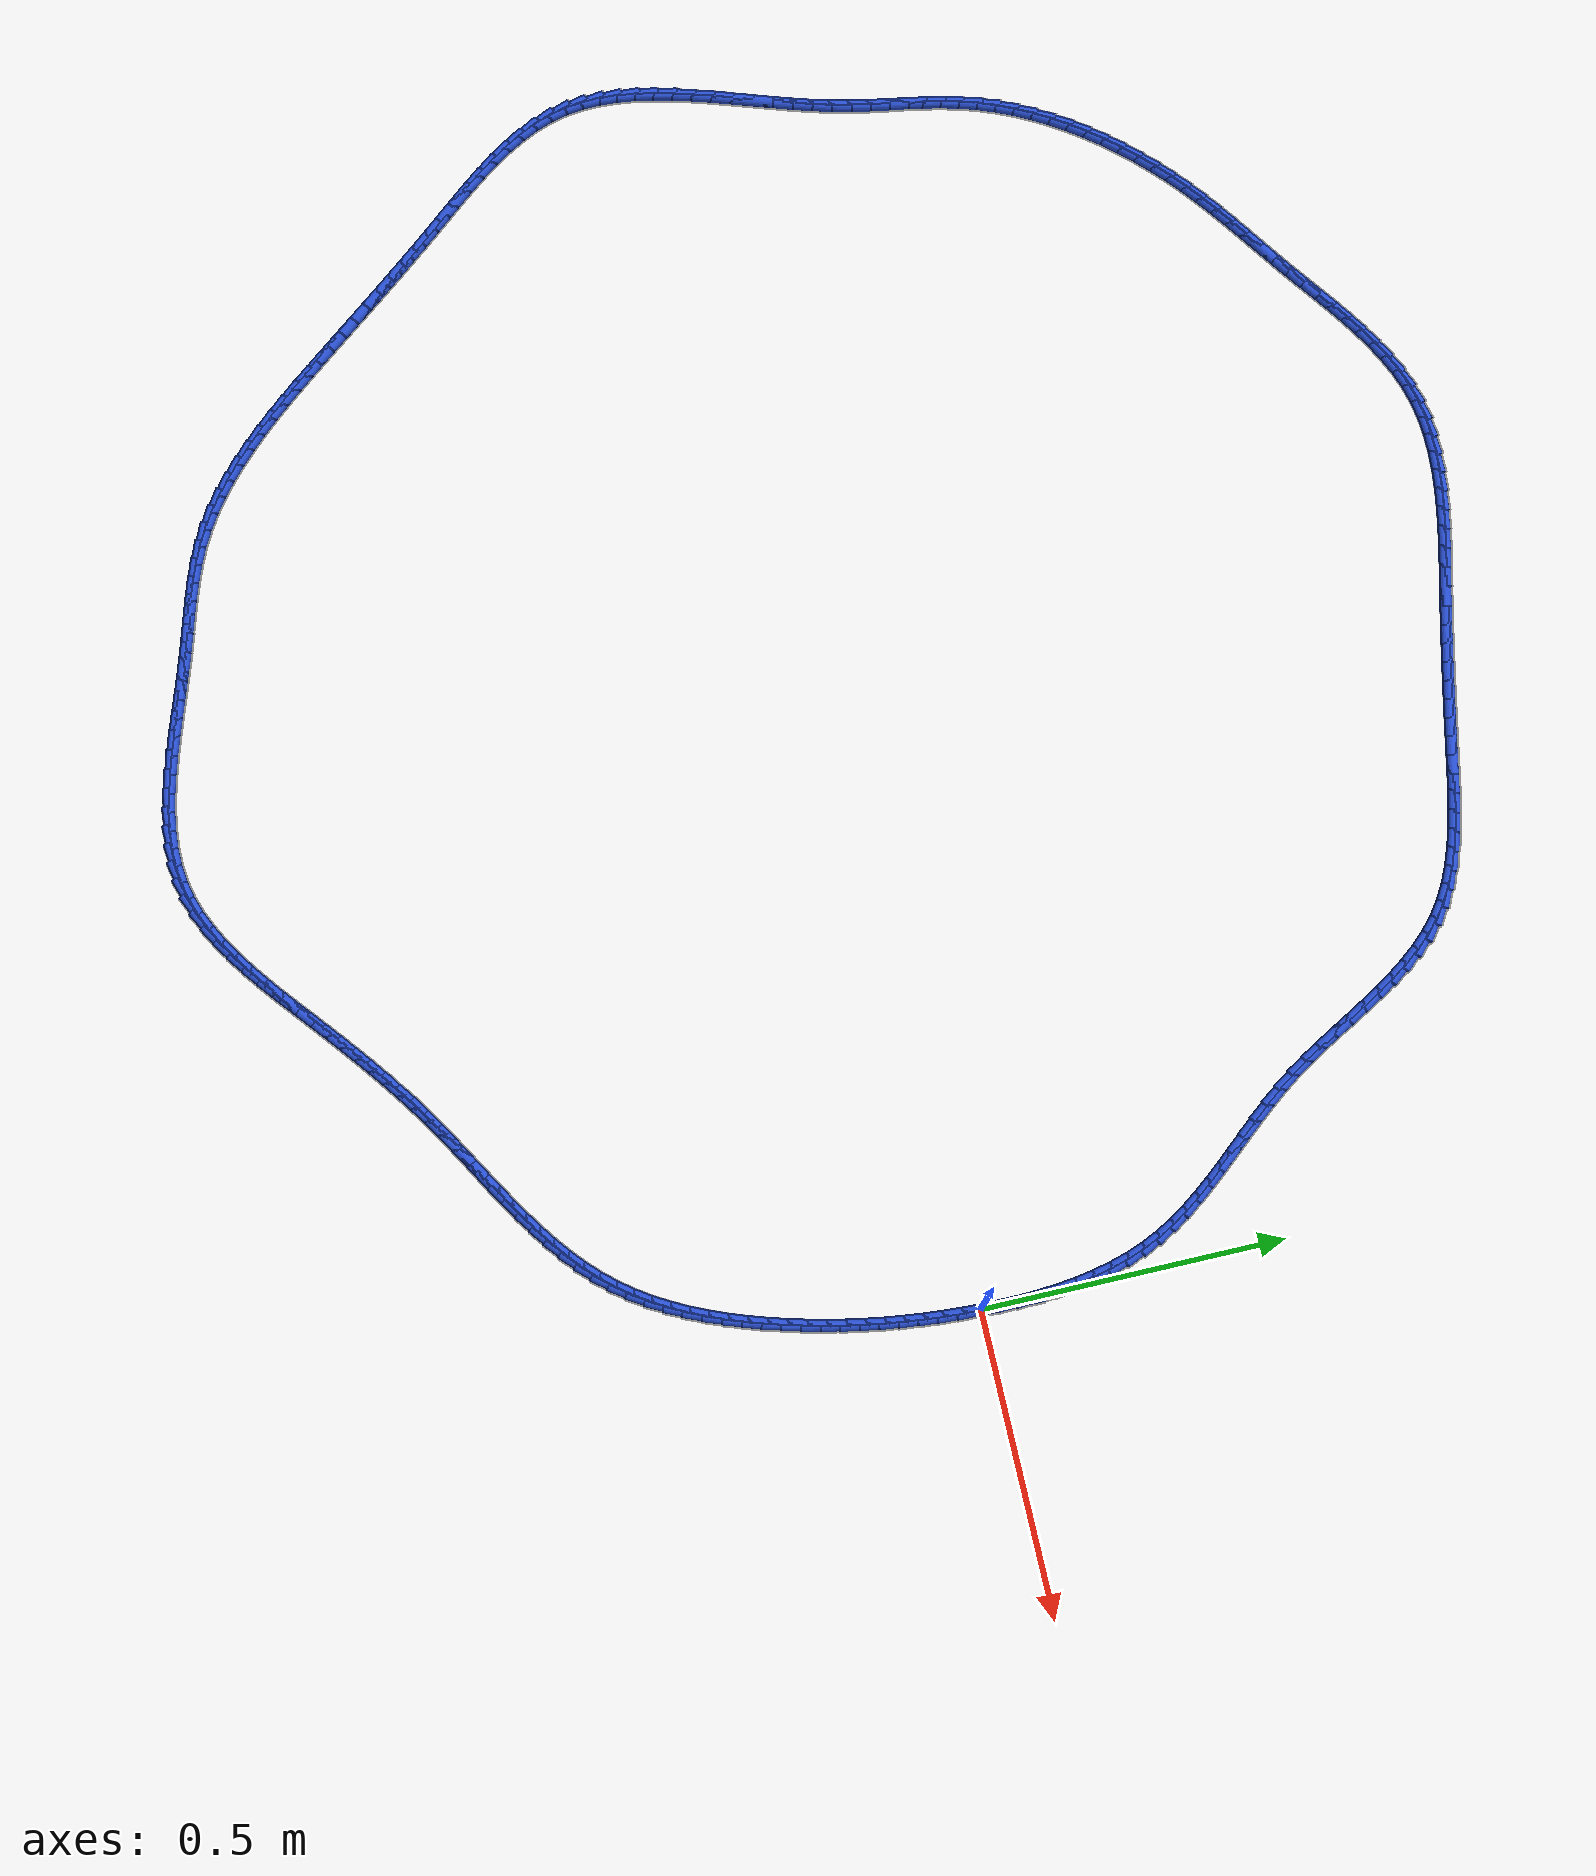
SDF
<sdf version="1.6">
 <world name="default">
  <light name="sun" type="directional">
   <pose>0 0 10 0 -0 0</pose>
   <diffuse>0.8 0.8 0.8 1</diffuse>
   <specular>0.2 0.2 0.2 1</specular>
   <attenuation>
    <range>1000</range>
    <constant>0.9</constant>
    <linear>0.01</linear>
    <quadratic>0.001</quadratic>
   </attenuation>
   <direction>-0.5 0.1 -0.9</direction>
  </light>
  <model name="ground_plane">
   <static>1</static>
   <link name="link">
    <collision name="collision">
     <geometry><plane><normal>0 0 1</normal><size>100 100</size></plane></geometry>
     <surface><friction><ode><mu>100</mu><mu2>50</mu2></ode></friction></surface>
    </collision>
    <visual name="visual">
     <cast_shadows>0</cast_shadows>
     <geometry><plane><normal>0 0 1</normal><size>100 100</size></plane></geometry>
     <material>
      <script><uri>file://media/materials/scripts/gazebo.material</uri><name>Gazebo/WhiteGlow</name></script>
     </material>
    </visual>
   </link>
  </model>
  <gravity>0 0 -9.8</gravity>
  <magnetic_field>6e-06 2.3e-05 -4.2e-05</magnetic_field>
  <atmosphere type="adiabatic"/>
  <physics name="default_physics" default="0" type="ode">
   <max_step_size>0.001</max_step_size>
   <real_time_factor>1</real_time_factor>
   <real_time_update_rate>1000</real_time_update_rate>
  </physics>
  <scene><ambient>0.4 0.4 0.4 1</ambient><background>0.7 0.7 0.7 1</background><shadows>1</shadows></scene>
  <spherical_coordinates>
   <surface_model>EARTH_WGS84</surface_model>
   <latitude_deg>0</latitude_deg>
   <longitude_deg>0</longitude_deg>
   <elevation>0</elevation>
   <heading_deg>0</heading_deg>
  </spherical_coordinates>
  <model name="line">
   <link name="link_0">
    <pose>-4.7704895589362195e-18 6.938893903907228e-17 0.01 0 1.57 1.5479829463222914</pose>
    <collision name="collision">
     <geometry><cylinder><radius>0.01</radius><length>0.08</length></cylinder></geometry>
    </collision>
    <visual name="visual">
     <material>
      <script><name>Gazebo/Blue</name><uri>file://media/materials/scripts/gazebo.material</uri></script>
     </material>
     <geometry><cylinder><radius>0.01</radius><length>0.08</length></cylinder></geometry>
    </visual>
   </link>
   <link name="link_1">
    <pose>0.0007215652060651547 0.031623547547972954 0.01 0 1.57 -1.566752087686649</pose>
    <collision name="collision">
     <geometry><cylinder><radius>0.01</radius><length>0.08</length></cylinder></geometry>
    </collision>
    <visual name="visual">
     <material>
      <script><name>Gazebo/Blue</name><uri>file://media/materials/scripts/gazebo.material</uri></script>
     </material>
     <geometry><cylinder><radius>0.01</radius><length>0.08</length></cylinder></geometry>
    </visual>
   </link>
   <link name="link_2">
    <pose>0.0005930693446006309 0.0633959421741575 0.01 0 1.57 -1.5352560706885645</pose>
    <collision name="collision">
     <geometry><cylinder><radius>0.01</radius><length>0.08</length></cylinder></geometry>
    </collision>
    <visual name="visual">
     <material>
      <script><name>Gazebo/Blue</name><uri>file://media/materials/scripts/gazebo.material</uri></script>
     </material>
     <geometry><cylinder><radius>0.01</radius><length>0.08</length></cylinder></geometry>
    </visual>
   </link>
   <link name="link_3">
    <pose>-0.000536455515506556 0.09516412204797578 0.01 0 1.57 -1.4987461094732293</pose>
    <collision name="collision">
     <geometry><cylinder><radius>0.01</radius><length>0.08</length></cylinder></geometry>
    </collision>
    <visual name="visual">
     <material>
      <script><name>Gazebo/Blue</name><uri>file://media/materials/scripts/gazebo.material</uri></script>
     </material>
     <geometry><cylinder><radius>0.01</radius><length>0.08</length></cylinder></geometry>
    </visual>
   </link>
   <link name="link_4">
    <pose>-0.0028179773053693853 0.12677502533884982 0.01 0 1.57 -1.4567747647652383</pose>
    <collision name="collision">
     <geometry><cylinder><radius>0.01</radius><length>0.08</length></cylinder></geometry>
    </collision>
    <visual name="visual">
     <material>
      <script><name>Gazebo/Blue</name><uri>file://media/materials/scripts/gazebo.material</uri></script>
     </material>
     <geometry><cylinder><radius>0.01</radius><length>0.08</length></cylinder></geometry>
    </visual>
   </link>
   <link name="link_5">
    <pose>-0.006402463956100846 0.15807559021620174 0.01 0 1.57 -1.4088394910362252</pose>
    <collision name="collision">
     <geometry><cylinder><radius>0.01</radius><length>0.08</length></cylinder></geometry>
    </collision>
    <visual name="visual">
     <material>
      <script><name>Gazebo/Blue</name><uri>file://media/materials/scripts/gazebo.material</uri></script>
     </material>
     <geometry><cylinder><radius>0.01</radius><length>0.08</length></cylinder></geometry>
    </visual>
   </link>
   <link name="link_6">
    <pose>-0.011440883398813911 0.1889127548494536 0.01 0 1.57 -1.3544112373524395</pose>
    <collision name="collision">
     <geometry><cylinder><radius>0.01</radius><length>0.08</length></cylinder></geometry>
    </collision>
    <visual name="visual">
     <material>
      <script><name>Gazebo/Blue</name><uri>file://media/materials/scripts/gazebo.material</uri></script>
     </material>
     <geometry><cylinder><radius>0.01</radius><length>0.08</length></cylinder></geometry>
    </visual>
   </link>
   <link name="link_7">
    <pose>-0.01808420356462158 0.2191334574080274 0.01 0 1.57 -1.2929812264186957</pose>
    <collision name="collision">
     <geometry><cylinder><radius>0.01</radius><length>0.08</length></cylinder></geometry>
    </collision>
    <visual name="visual">
     <material>
      <script><name>Gazebo/Blue</name><uri>file://media/materials/scripts/gazebo.material</uri></script>
     </material>
     <geometry><cylinder><radius>0.01</radius><length>0.08</length></cylinder></geometry>
    </visual>
   </link>
   <link name="link_8">
    <pose>-0.026483392384636803 0.24858463606134518 0.01 0 1.57 -1.2241323928483854</pose>
    <collision name="collision">
     <geometry><cylinder><radius>0.01</radius><length>0.08</length></cylinder></geometry>
    </collision>
    <visual name="visual">
     <material>
      <script><name>Gazebo/Blue</name><uri>file://media/materials/scripts/gazebo.material</uri></script>
     </material>
     <geometry><cylinder><radius>0.01</radius><length>0.08</length></cylinder></geometry>
    </visual>
   </link>
   <link name="link_9">
    <pose>-0.036789417789972585 0.2771132289788292 0.01 0 1.57 -1.1477855805589992</pose>
    <collision name="collision">
     <geometry><cylinder><radius>0.01</radius><length>0.08</length></cylinder></geometry>
    </collision>
    <visual name="visual">
     <material>
      <script><name>Gazebo/Blue</name><uri>file://media/materials/scripts/gazebo.material</uri></script>
     </material>
     <geometry><cylinder><radius>0.01</radius><length>0.08</length></cylinder></geometry>
    </visual>
   </link>
   <link name="link_10">
    <pose>-0.04914966944523792 0.30456894852390776 0.01 0 1.57 -1.0713675540776297</pose>
    <collision name="collision">
     <geometry><cylinder><radius>0.01</radius><length>0.08</length></cylinder></geometry>
    </collision>
    <visual name="visual">
     <material>
      <script><name>Gazebo/Blue</name><uri>file://media/materials/scripts/gazebo.material</uri></script>
     </material>
     <geometry><cylinder><radius>0.01</radius><length>0.08</length></cylinder></geometry>
    </visual>
   </link>
   <link name="link_11">
    <pose>-0.06353556231688706 0.33093793847237124 0.01 0 1.57 -1.006141260931769</pose>
    <collision name="collision">
     <geometry><cylinder><radius>0.01</radius><length>0.08</length></cylinder></geometry>
    </collision>
    <visual name="visual">
     <material>
      <script><name>Gazebo/Blue</name><uri>file://media/materials/scripts/gazebo.material</uri></script>
     </material>
     <geometry><cylinder><radius>0.01</radius><length>0.08</length></cylinder></geometry>
    </visual>
   </link>
   <link name="link_12">
    <pose>-0.07966595244275039 0.356402148995462 0.01 0 1.57 -0.9534685735608708</pose>
    <collision name="collision">
     <geometry><cylinder><radius>0.01</radius><length>0.08</length></cylinder></geometry>
    </collision>
    <visual name="visual">
     <material>
      <script><name>Gazebo/Blue</name><uri>file://media/materials/scripts/gazebo.material</uri></script>
     </material>
     <geometry><cylinder><radius>0.01</radius><length>0.08</length></cylinder></geometry>
    </visual>
   </link>
   <link name="link_13">
    <pose>-0.09724017118786986 0.38115866754672745 0.01 0 1.57 -0.9133753165994942</pose>
    <collision name="collision">
     <geometry><cylinder><radius>0.01</radius><length>0.08</length></cylinder></geometry>
    </collision>
    <visual name="visual">
     <material>
      <script><name>Gazebo/Blue</name><uri>file://media/materials/scripts/gazebo.material</uri></script>
     </material>
     <geometry><cylinder><radius>0.01</radius><length>0.08</length></cylinder></geometry>
    </visual>
   </link>
   <link name="link_14">
    <pose>-0.11595754991728757 0.4054045815797148 0.01 0 1.57 -0.8855972150997148</pose>
    <collision name="collision">
     <geometry><cylinder><radius>0.01</radius><length>0.08</length></cylinder></geometry>
    </collision>
    <visual name="visual">
     <material>
      <script><name>Gazebo/Blue</name><uri>file://media/materials/scripts/gazebo.material</uri></script>
     </material>
     <geometry><cylinder><radius>0.01</radius><length>0.08</length></cylinder></geometry>
    </visual>
   </link>
   <link name="link_15">
    <pose>-0.13551741999604533 0.4293369785479711 0.01 0 1.57 -0.869770980029541</pose>
    <collision name="collision">
     <geometry><cylinder><radius>0.01</radius><length>0.08</length></cylinder></geometry>
    </collision>
    <visual name="visual">
     <material>
      <script><name>Gazebo/Blue</name><uri>file://media/materials/scripts/gazebo.material</uri></script>
     </material>
     <geometry><cylinder><radius>0.01</radius><length>0.08</length></cylinder></geometry>
    </visual>
   </link>
   <link name="link_16">
    <pose>-0.1556191127891852 0.45315294590504357 0.01 0 1.57 -0.8655565255962655</pose>
    <collision name="collision">
     <geometry><cylinder><radius>0.01</radius><length>0.08</length></cylinder></geometry>
    </collision>
    <visual name="visual">
     <material>
      <script><name>Gazebo/Blue</name><uri>file://media/materials/scripts/gazebo.material</uri></script>
     </material>
     <geometry><cylinder><radius>0.01</radius><length>0.08</length></cylinder></geometry>
    </visual>
   </link>
   <link name="link_17">
    <pose>-0.17596195966174907 0.4770495711044794 0.01 0 1.57 -0.872697957210107</pose>
    <collision name="collision">
     <geometry><cylinder><radius>0.01</radius><length>0.08</length></cylinder></geometry>
    </collision>
    <visual name="visual">
     <material>
      <script><name>Gazebo/Blue</name><uri>file://media/materials/scripts/gazebo.material</uri></script>
     </material>
     <geometry><cylinder><radius>0.01</radius><length>0.08</length></cylinder></geometry>
    </visual>
   </link>
   <link name="link_18">
    <pose>-0.19624529197877905 0.501223941599826 0.01 0 1.57 -0.8910345357654627</pose>
    <collision name="collision">
     <geometry><cylinder><radius>0.01</radius><length>0.08</length></cylinder></geometry>
    </collision>
    <visual name="visual">
     <material>
      <script><name>Gazebo/Blue</name><uri>file://media/materials/scripts/gazebo.material</uri></script>
     </material>
     <geometry><cylinder><radius>0.01</radius><length>0.08</length></cylinder></geometry>
    </visual>
   </link>
   <link name="link_19">
    <pose>-0.21616844110531708 0.5258731448446303 0.01 0 1.57 -0.920469339215087</pose>
    <collision name="collision">
     <geometry><cylinder><radius>0.01</radius><length>0.08</length></cylinder></geometry>
    </collision>
    <visual name="visual">
     <material>
      <script><name>Gazebo/Blue</name><uri>file://media/materials/scripts/gazebo.material</uri></script>
     </material>
     <geometry><cylinder><radius>0.01</radius><length>0.08</length></cylinder></geometry>
    </visual>
   </link>
   <link name="link_20">
    <pose>-0.235430738406405 0.5511942682924398 0.01 0 1.57 -0.96083028017635</pose>
    <collision name="collision">
     <geometry><cylinder><radius>0.01</radius><length>0.08</length></cylinder></geometry>
    </collision>
    <visual name="visual">
     <material>
      <script><name>Gazebo/Blue</name><uri>file://media/materials/scripts/gazebo.material</uri></script>
     </material>
     <geometry><cylinder><radius>0.01</radius><length>0.08</length></cylinder></geometry>
    </visual>
   </link>
   <link name="link_21">
    <pose>-0.25373319038439 0.5773829669955516 0.01 0 1.57 -1.0042836720142712</pose>
    <collision name="collision">
     <geometry><cylinder><radius>0.01</radius><length>0.08</length></cylinder></geometry>
    </collision>
    <visual name="visual">
     <material>
      <script><name>Gazebo/Blue</name><uri>file://media/materials/scripts/gazebo.material</uri></script>
     </material>
     <geometry><cylinder><radius>0.01</radius><length>0.08</length></cylinder></geometry>
    </visual>
   </link>
   <link name="link_22">
    <pose>-0.2709647914809507 0.6044741484911897 0.01 0 1.57 -1.0364075297354607</pose>
    <collision name="collision">
     <geometry><cylinder><radius>0.01</radius><length>0.08</length></cylinder></geometry>
    </collision>
    <visual name="visual">
     <material>
      <script><name>Gazebo/Blue</name><uri>file://media/materials/scripts/gazebo.material</uri></script>
     </material>
     <geometry><cylinder><radius>0.01</radius><length>0.08</length></cylinder></geometry>
    </visual>
   </link>
   <link name="link_23">
    <pose>-0.2873719839273866 0.6321970685595827 0.01 0 1.57 -1.0559378814561677</pose>
    <collision name="collision">
     <geometry><cylinder><radius>0.01</radius><length>0.08</length></cylinder></geometry>
    </collision>
    <visual name="visual">
     <material>
      <script><name>Gazebo/Blue</name><uri>file://media/materials/scripts/gazebo.material</uri></script>
     </material>
     <geometry><cylinder><radius>0.01</radius><length>0.08</length></cylinder></geometry>
    </visual>
   </link>
   <link name="link_24">
    <pose>-0.30324123016649535 0.6602467619050015 0.01 0 1.57 -1.0630859813531304</pose>
    <collision name="collision">
     <geometry><cylinder><radius>0.01</radius><length>0.08</length></cylinder></geometry>
    </collision>
    <visual name="visual">
     <material>
      <script><name>Gazebo/Blue</name><uri>file://media/materials/scripts/gazebo.material</uri></script>
     </material>
     <geometry><cylinder><radius>0.01</radius><length>0.08</length></cylinder></geometry>
    </visual>
   </link>
   <link name="link_25">
    <pose>-0.31885899264107476 0.6883182632317167 0.01 0 1.57 -1.057811188708045</pose>
    <collision name="collision">
     <geometry><cylinder><radius>0.01</radius><length>0.08</length></cylinder></geometry>
    </collision>
    <visual name="visual">
     <material>
      <script><name>Gazebo/Blue</name><uri>file://media/materials/scripts/gazebo.material</uri></script>
     </material>
     <geometry><cylinder><radius>0.01</radius><length>0.08</length></cylinder></geometry>
    </visual>
   </link>
   <link name="link_26">
    <pose>-0.33451173379392257 0.7161066072439994 0.01 0 1.57 -1.0397812821511725</pose>
    <collision name="collision">
     <geometry><cylinder><radius>0.01</radius><length>0.08</length></cylinder></geometry>
    </collision>
    <visual name="visual">
     <material>
      <script><name>Gazebo/Blue</name><uri>file://media/materials/scripts/gazebo.material</uri></script>
     </material>
     <geometry><cylinder><radius>0.01</radius><length>0.08</length></cylinder></geometry>
    </visual>
   </link>
   <link name="link_27">
    <pose>-0.3504859160678367 0.7433068286461207 0.01 0 1.57 -1.008375818661642</pose>
    <collision name="collision">
     <geometry><cylinder><radius>0.01</radius><length>0.08</length></cylinder></geometry>
    </collision>
    <visual name="visual">
     <material>
      <script><name>Gazebo/Blue</name><uri>file://media/materials/scripts/gazebo.material</uri></script>
     </material>
     <geometry><cylinder><radius>0.01</radius><length>0.08</length></cylinder></geometry>
    </visual>
   </link>
   <link name="link_28">
    <pose>-0.3670680019056146 0.7696139621423512 0.01 0 1.57 -0.962745701899153</pose>
    <collision name="collision">
     <geometry><cylinder><radius>0.01</radius><length>0.08</length></cylinder></geometry>
    </collision>
    <visual name="visual">
     <material>
      <script><name>Gazebo/Blue</name><uri>file://media/materials/scripts/gazebo.material</uri></script>
     </material>
     <geometry><cylinder><radius>0.01</radius><length>0.08</length></cylinder></geometry>
    </visual>
   </link>
   <link name="link_29">
    <pose>-0.3845444537500541 0.7947230424369613 0.01 0 1.57 -0.9019613113625815</pose>
    <collision name="collision">
     <geometry><cylinder><radius>0.01</radius><length>0.08</length></cylinder></geometry>
    </collision>
    <visual name="visual">
     <material>
      <script><name>Gazebo/Blue</name><uri>file://media/materials/scripts/gazebo.material</uri></script>
     </material>
     <geometry><cylinder><radius>0.01</radius><length>0.08</length></cylinder></geometry>
    </visual>
   </link>
   <link name="link_30">
    <pose>-0.40320173404395304 0.8183291042342227 0.01 0 1.57 -0.8252958983222832</pose>
    <collision name="collision">
     <geometry><cylinder><radius>0.01</radius><length>0.08</length></cylinder></geometry>
    </collision>
    <visual name="visual">
     <material>
      <script><name>Gazebo/Blue</name><uri>file://media/materials/scripts/gazebo.material</uri></script>
     </material>
     <geometry><cylinder><radius>0.01</radius><length>0.08</length></cylinder></geometry>
    </visual>
   </link>
   <link name="link_31">
    <pose>-0.42332630523010895 0.8401271822384054 0.01 0 1.57 -0.7326796513070319</pose>
    <collision name="collision">
     <geometry><cylinder><radius>0.01</radius><length>0.08</length></cylinder></geometry>
    </collision>
    <visual name="visual">
     <material>
      <script><name>Gazebo/Blue</name><uri>file://media/materials/scripts/gazebo.material</uri></script>
     </material>
     <geometry><cylinder><radius>0.01</radius><length>0.08</length></cylinder></geometry>
    </visual>
   </link>
   <link name="link_32">
    <pose>-0.44520462975131975 0.8598123111537808 0.01 0 1.57 -0.6261209004929671</pose>
    <collision name="collision">
     <geometry><cylinder><radius>0.01</radius><length>0.08</length></cylinder></geometry>
    </collision>
    <visual name="visual">
     <material>
      <script><name>Gazebo/Blue</name><uri>file://media/materials/scripts/gazebo.material</uri></script>
     </material>
     <geometry><cylinder><radius>0.01</radius><length>0.08</length></cylinder></geometry>
    </visual>
   </link>
   <link name="link_33">
    <pose>-0.4691055232478807 0.8770972029817375 0.01 0 1.57 -0.5225299405900189</pose>
    <collision name="collision">
     <geometry><cylinder><radius>0.01</radius><length>0.08</length></cylinder></geometry>
    </collision>
    <visual name="visual">
     <material>
      <script><name>Gazebo/Blue</name><uri>file://media/materials/scripts/gazebo.material</uri></script>
     </material>
     <geometry><cylinder><radius>0.01</radius><length>0.08</length></cylinder></geometry>
    </visual>
   </link>
   <link name="link_34">
    <pose>-0.494988831148285 0.8920040738524632 0.01 0 1.57 -0.43520205764031294</pose>
    <collision name="collision">
     <geometry><cylinder><radius>0.01</radius><length>0.08</length></cylinder></geometry>
    </collision>
    <visual name="visual">
     <material>
      <script><name>Gazebo/Blue</name><uri>file://media/materials/scripts/gazebo.material</uri></script>
     </material>
     <geometry><cylinder><radius>0.01</radius><length>0.08</length></cylinder></geometry>
    </visual>
   </link>
   <link name="link_35">
    <pose>-0.5225512562623872 0.9048187372392548 0.01 0 1.57 -0.3638521827705602</pose>
    <collision name="collision">
     <geometry><cylinder><radius>0.01</radius><length>0.08</length></cylinder></geometry>
    </collision>
    <visual name="visual">
     <material>
      <script><name>Gazebo/Blue</name><uri>file://media/materials/scripts/gazebo.material</uri></script>
     </material>
     <geometry><cylinder><radius>0.01</radius><length>0.08</length></cylinder></geometry>
    </visual>
   </link>
   <link name="link_36">
    <pose>-0.5514810942387424 0.9158354283047339 0.01 0 1.57 -0.3072075897965701</pose>
    <collision name="collision">
     <geometry><cylinder><radius>0.01</radius><length>0.08</length></cylinder></geometry>
    </collision>
    <visual name="visual">
     <material>
      <script><name>Gazebo/Blue</name><uri>file://media/materials/scripts/gazebo.material</uri></script>
     </material>
     <geometry><cylinder><radius>0.01</radius><length>0.08</length></cylinder></geometry>
    </visual>
   </link>
   <link name="link_37">
    <pose>-0.5814666407259056 0.9253483822115213 0.01 0 1.57 -0.26390816279050633</pose>
    <collision name="collision">
     <geometry><cylinder><radius>0.01</radius><length>0.08</length></cylinder></geometry>
    </collision>
    <visual name="visual">
     <material>
      <script><name>Gazebo/Blue</name><uri>file://media/materials/scripts/gazebo.material</uri></script>
     </material>
     <geometry><cylinder><radius>0.01</radius><length>0.08</length></cylinder></geometry>
    </visual>
   </link>
   <link name="link_38">
    <pose>-0.6121961913724312 0.9336518341222371 0.01 0 1.57 -0.232792323611954</pose>
    <collision name="collision">
     <geometry><cylinder><radius>0.01</radius><length>0.08</length></cylinder></geometry>
    </collision>
    <visual name="visual">
     <material>
      <script><name>Gazebo/Blue</name><uri>file://media/materials/scripts/gazebo.material</uri></script>
     </material>
     <geometry><cylinder><radius>0.01</radius><length>0.08</length></cylinder></geometry>
    </visual>
   </link>
   <link name="link_39">
    <pose>-0.6433580418268743 0.941040019199503 0.01 0 1.57 -0.21304160974595207</pose>
    <collision name="collision">
     <geometry><cylinder><radius>0.01</radius><length>0.08</length></cylinder></geometry>
    </collision>
    <visual name="visual">
     <material>
      <script><name>Gazebo/Blue</name><uri>file://media/materials/scripts/gazebo.material</uri></script>
     </material>
     <geometry><cylinder><radius>0.01</radius><length>0.08</length></cylinder></geometry>
    </visual>
   </link>
   <link name="link_40">
    <pose>-0.6746404877377898 0.9478071726059394 0.01 0 1.57 -0.20425041362675309</pose>
    <collision name="collision">
     <geometry><cylinder><radius>0.01</radius><length>0.08</length></cylinder></geometry>
    </collision>
    <visual name="visual">
     <material>
      <script><name>Gazebo/Blue</name><uri>file://media/materials/scripts/gazebo.material</uri></script>
     </material>
     <geometry><cylinder><radius>0.01</radius><length>0.08</length></cylinder></geometry>
    </visual>
   </link>
   <link name="link_41">
    <pose>-0.7057319850688487 0.954247432624783 0.01 0 1.57 -0.203951934197933</pose>
    <collision name="collision">
     <geometry><cylinder><radius>0.01</radius><length>0.08</length></cylinder></geometry>
    </collision>
    <visual name="visual">
     <material>
      <script><name>Gazebo/Blue</name><uri>file://media/materials/scripts/gazebo.material</uri></script>
     </material>
     <geometry><cylinder><radius>0.01</radius><length>0.08</length></cylinder></geometry>
    </visual>
   </link>
   <link name="link_42">
    <pose>-0.7364206675993615 0.9605947016384856 0.01 0 1.57 -0.20551247004671597</pose>
    <collision name="collision">
     <geometry><cylinder><radius>0.01</radius><length>0.08</length></cylinder></geometry>
    </collision>
    <visual name="visual">
     <material>
      <script><name>Gazebo/Blue</name><uri>file://media/materials/scripts/gazebo.material</uri></script>
     </material>
     <geometry><cylinder><radius>0.01</radius><length>0.08</length></cylinder></geometry>
    </visual>
   </link>
   <link name="link_43">
    <pose>-0.7667642308547358 0.9669199842524087 0.01 0 1.57 -0.20781201566636634</pose>
    <collision name="collision">
     <geometry><cylinder><radius>0.01</radius><length>0.08</length></cylinder></geometry>
    </collision>
    <visual name="visual">
     <material>
      <script><name>Gazebo/Blue</name><uri>file://media/materials/scripts/gazebo.material</uri></script>
     </material>
     <geometry><cylinder><radius>0.01</radius><length>0.08</length></cylinder></geometry>
    </visual>
   </link>
   <link name="link_44">
    <pose>-0.7968654899333169 0.973267019043846 0.01 0 1.57 -0.2108427023587976</pose>
    <collision name="collision">
     <geometry><cylinder><radius>0.01</radius><length>0.08</length></cylinder></geometry>
    </collision>
    <visual name="visual">
     <material>
      <script><name>Gazebo/Blue</name><uri>file://media/materials/scripts/gazebo.material</uri></script>
     </material>
     <geometry><cylinder><radius>0.01</radius><length>0.08</length></cylinder></geometry>
    </visual>
   </link>
   <link name="link_45">
    <pose>-0.8268272599334493 0.9796795445900913 0.01 0 1.57 -0.2145807131898262</pose>
    <collision name="collision">
     <geometry><cylinder><radius>0.01</radius><length>0.08</length></cylinder></geometry>
    </collision>
    <visual name="visual">
     <material>
      <script><name>Gazebo/Blue</name><uri>file://media/materials/scripts/gazebo.material</uri></script>
     </material>
     <geometry><cylinder><radius>0.01</radius><length>0.08</length></cylinder></geometry>
    </visual>
   </link>
   <link name="link_46">
    <pose>-0.8567523559534792 0.986201299468439 0.01 0 1.57 -0.21898677206744444</pose>
    <collision name="collision">
     <geometry><cylinder><radius>0.01</radius><length>0.08</length></cylinder></geometry>
    </collision>
    <visual name="visual">
     <material>
      <script><name>Gazebo/Blue</name><uri>file://media/materials/scripts/gazebo.material</uri></script>
     </material>
     <geometry><cylinder><radius>0.01</radius><length>0.08</length></cylinder></geometry>
    </visual>
   </link>
   <link name="link_47">
    <pose>-0.8867435930917515 0.9928760222561825 0.01 0 1.57 -0.22400746100928717</pose>
    <collision name="collision">
     <geometry><cylinder><radius>0.01</radius><length>0.08</length></cylinder></geometry>
    </collision>
    <visual name="visual">
     <material>
      <script><name>Gazebo/Blue</name><uri>file://media/materials/scripts/gazebo.material</uri></script>
     </material>
     <geometry><cylinder><radius>0.01</radius><length>0.08</length></cylinder></geometry>
    </visual>
   </link>
   <link name="link_48">
    <pose>-0.9169037864466116 0.9997474515306161 0.01 0 1.57 -0.22957727754355314</pose>
    <collision name="collision">
     <geometry><cylinder><radius>0.01</radius><length>0.08</length></cylinder></geometry>
    </collision>
    <visual name="visual">
     <material>
      <script><name>Gazebo/Blue</name><uri>file://media/materials/scripts/gazebo.material</uri></script>
     </material>
     <geometry><cylinder><radius>0.01</radius><length>0.08</length></cylinder></geometry>
    </visual>
   </link>
   <link name="link_49">
    <pose>-0.9473357511164046 1.0068593258690335 0.01 0 1.57 -0.23473273797342897</pose>
    <collision name="collision">
     <geometry><cylinder><radius>0.01</radius><length>0.08</length></cylinder></geometry>
    </collision>
    <visual name="visual">
     <material>
      <script><name>Gazebo/Blue</name><uri>file://media/materials/scripts/gazebo.material</uri></script>
     </material>
     <geometry><cylinder><radius>0.01</radius><length>0.08</length></cylinder></geometry>
    </visual>
   </link>
   <link name="link_50">
    <pose>-0.9781215209429756 1.0142214699397796 0.01 0 1.57 -0.23399018855294518</pose>
    <collision name="collision">
     <geometry><cylinder><radius>0.01</radius><length>0.08</length></cylinder></geometry>
    </collision>
    <visual name="visual">
     <material>
      <script><name>Gazebo/Blue</name><uri>file://media/materials/scripts/gazebo.material</uri></script>
     </material>
     <geometry><cylinder><radius>0.01</radius><length>0.08</length></cylinder></geometry>
    </visual>
   </link>
   <link name="link_51">
    <pose>-1.0092136997729113 1.0216324855202985 0.01 0 1.57 -0.22539997940004383</pose>
    <collision name="collision">
     <geometry><cylinder><radius>0.01</radius><length>0.08</length></cylinder></geometry>
    </collision>
    <visual name="visual">
     <material>
      <script><name>Gazebo/Blue</name><uri>file://media/materials/scripts/gazebo.material</uri></script>
     </material>
     <geometry><cylinder><radius>0.01</radius><length>0.08</length></cylinder></geometry>
    </visual>
   </link>
   <link name="link_52">
    <pose>-1.0405151461079742 1.028809792622391 0.01 0 1.57 -0.20894333708750915</pose>
    <collision name="collision">
     <geometry><cylinder><radius>0.01</radius><length>0.08</length></cylinder></geometry>
    </collision>
    <visual name="visual">
     <material>
      <script><name>Gazebo/Blue</name><uri>file://media/materials/scripts/gazebo.material</uri></script>
     </material>
     <geometry><cylinder><radius>0.01</radius><length>0.08</length></cylinder></geometry>
    </visual>
   </link>
   <link name="link_53">
    <pose>-1.0719286150847553 1.0354706425713736 0.01 0 1.57 -0.18439022737342584</pose>
    <collision name="collision">
     <geometry><cylinder><radius>0.01</radius><length>0.08</length></cylinder></geometry>
    </collision>
    <visual name="visual">
     <material>
      <script><name>Gazebo/Blue</name><uri>file://media/materials/scripts/gazebo.material</uri></script>
     </material>
     <geometry><cylinder><radius>0.01</radius><length>0.08</length></cylinder></geometry>
    </visual>
   </link>
   <link name="link_54">
    <pose>-1.1033568618398422 1.0413322866925612 0.01 0 1.57 -0.15131714291794712</pose>
    <collision name="collision">
     <geometry><cylinder><radius>0.01</radius><length>0.08</length></cylinder></geometry>
    </collision>
    <visual name="visual">
     <material>
      <script><name>Gazebo/Blue</name><uri>file://media/materials/scripts/gazebo.material</uri></script>
     </material>
     <geometry><cylinder><radius>0.01</radius><length>0.08</length></cylinder></geometry>
    </visual>
   </link>
   <link name="link_55">
    <pose>-1.1347026415098243 1.046111976311271 0.01 0 1.57 -0.1091384651255456</pose>
    <collision name="collision">
     <geometry><cylinder><radius>0.01</radius><length>0.08</length></cylinder></geometry>
    </collision>
    <visual name="visual">
     <material>
      <script><name>Gazebo/Blue</name><uri>file://media/materials/scripts/gazebo.material</uri></script>
     </material>
     <geometry><cylinder><radius>0.01</radius><length>0.08</length></cylinder></geometry>
    </visual>
   </link>
   <link name="link_56">
    <pose>-1.1658687092312914 1.0495269627528183 0.01 0 1.57 -0.05715959908341486</pose>
    <collision name="collision">
     <geometry><cylinder><radius>0.01</radius><length>0.08</length></cylinder></geometry>
    </collision>
    <visual name="visual">
     <material>
      <script><name>Gazebo/Blue</name><uri>file://media/materials/scripts/gazebo.material</uri></script>
     </material>
     <geometry><cylinder><radius>0.01</radius><length>0.08</length></cylinder></geometry>
    </visual>
   </link>
   <link name="link_57">
    <pose>-1.1967578201408324 1.0512944973425193 0.01 0 1.57 0.005330653118221719</pose>
    <collision name="collision">
     <geometry><cylinder><radius>0.01</radius><length>0.08</length></cylinder></geometry>
    </collision>
    <visual name="visual">
     <material>
      <script><name>Gazebo/Blue</name><uri>file://media/materials/scripts/gazebo.material</uri></script>
     </material>
     <geometry><cylinder><radius>0.01</radius><length>0.08</length></cylinder></geometry>
    </visual>
   </link>
   <link name="link_58">
    <pose>-1.2272727293750363 1.0511318314056906 0.01 0 1.57 0.07890842986414</pose>
    <collision name="collision">
     <geometry><cylinder><radius>0.01</radius><length>0.08</length></cylinder></geometry>
    </collision>
    <visual name="visual">
     <material>
      <script><name>Gazebo/Blue</name><uri>file://media/materials/scripts/gazebo.material</uri></script>
     </material>
     <geometry><cylinder><radius>0.01</radius><length>0.08</length></cylinder></geometry>
    </visual>
   </link>
   <link name="link_59">
    <pose>-1.2573161920704927 1.0487562162676474 0.01 0 1.57 0.16379003148570254</pose>
    <collision name="collision">
     <geometry><cylinder><radius>0.01</radius><length>0.08</length></cylinder></geometry>
    </collision>
    <visual name="visual">
     <material>
      <script><name>Gazebo/Blue</name><uri>file://media/materials/scripts/gazebo.material</uri></script>
     </material>
     <geometry><cylinder><radius>0.01</radius><length>0.08</length></cylinder></geometry>
    </visual>
   </link>
   <link name="link_60">
    <pose>-1.2867909633637906 1.0438849032537063 0.01 0 1.57 0.25888215036940543</pose>
    <collision name="collision">
     <geometry><cylinder><radius>0.01</radius><length>0.08</length></cylinder></geometry>
    </collision>
    <visual name="visual">
     <material>
      <script><name>Gazebo/Blue</name><uri>file://media/materials/scripts/gazebo.material</uri></script>
     </material>
     <geometry><cylinder><radius>0.01</radius><length>0.08</length></cylinder></geometry>
    </visual>
   </link>
   <link name="link_61">
    <pose>-1.315604862806702 1.036254264061032 0.01 0 1.57 0.35137744762221534</pose>
    <collision name="collision">
     <geometry><cylinder><radius>0.01</radius><length>0.08</length></cylinder></geometry>
    </collision>
    <visual name="visual">
     <material>
      <script><name>Gazebo/Blue</name><uri>file://media/materials/scripts/gazebo.material</uri></script>
     </material>
     <geometry><cylinder><radius>0.01</radius><length>0.08</length></cylinder></geometry>
    </visual>
   </link>
   <link name="link_62">
    <pose>-1.343754256049594 1.02593497045301 0.01 0 1.57 0.4304428778807871</pose>
    <collision name="collision">
     <geometry><cylinder><radius>0.01</radius><length>0.08</length></cylinder></geometry>
    </collision>
    <visual name="visual">
     <material>
      <script><name>Gazebo/Blue</name><uri>file://media/materials/scripts/gazebo.material</uri></script>
     </material>
     <geometry><cylinder><radius>0.01</radius><length>0.08</length></cylinder></geometry>
    </visual>
   </link>
   <link name="link_63">
    <pose>-1.3713108553698143 1.013282160508175 0.01 0 1.57 0.4957526891505219</pose>
    <collision name="collision">
     <geometry><cylinder><radius>0.01</radius><length>0.08</length></cylinder></geometry>
    </collision>
    <visual name="visual">
     <material>
      <script><name>Gazebo/Blue</name><uri>file://media/materials/scripts/gazebo.material</uri></script>
     </material>
     <geometry><cylinder><radius>0.01</radius><length>0.08</length></cylinder></geometry>
    </visual>
   </link>
   <link name="link_64">
    <pose>-1.398348775982786 0.9986600444423063 0.01 0 1.57 0.5478842681681275</pose>
    <collision name="collision">
     <geometry><cylinder><radius>0.01</radius><length>0.08</length></cylinder></geometry>
    </collision>
    <visual name="visual">
     <material>
      <script><name>Gazebo/Blue</name><uri>file://media/materials/scripts/gazebo.material</uri></script>
     </material>
     <geometry><cylinder><radius>0.01</radius><length>0.08</length></cylinder></geometry>
    </visual>
   </link>
   <link name="link_65">
    <pose>-1.4249421331039358 0.9824328324711838 0.01 0 1.57 0.5876370850014354</pose>
    <collision name="collision">
     <geometry><cylinder><radius>0.01</radius><length>0.08</length></cylinder></geometry>
    </collision>
    <visual name="visual">
     <material>
      <script><name>Gazebo/Blue</name><uri>file://media/materials/scripts/gazebo.material</uri></script>
     </material>
     <geometry><cylinder><radius>0.01</radius><length>0.08</length></cylinder></geometry>
    </visual>
   </link>
   <link name="link_66">
    <pose>-1.4511650419486888 0.9649647348105883 0.01 0 1.57 0.6157860353619142</pose>
    <collision name="collision">
     <geometry><cylinder><radius>0.01</radius><length>0.08</length></cylinder></geometry>
    </collision>
    <visual name="visual">
     <material>
      <script><name>Gazebo/Blue</name><uri>file://media/materials/scripts/gazebo.material</uri></script>
     </material>
     <geometry><cylinder><radius>0.01</radius><length>0.08</length></cylinder></geometry>
    </visual>
   </link>
   <link name="link_67">
    <pose>-1.4770916177324702 0.9466199616762998 0.01 0 1.57 0.6329354108801509</pose>
    <collision name="collision">
     <geometry><cylinder><radius>0.01</radius><length>0.08</length></cylinder></geometry>
    </collision>
    <visual name="visual">
     <material>
      <script><name>Gazebo/Blue</name><uri>file://media/materials/scripts/gazebo.material</uri></script>
     </material>
     <geometry><cylinder><radius>0.01</radius><length>0.08</length></cylinder></geometry>
    </visual>
   </link>
   <link name="link_68">
    <pose>-1.5027959756707054 0.9277627232840985 0.01 0 1.57 0.6394394249734369</pose>
    <collision name="collision">
     <geometry><cylinder><radius>0.01</radius><length>0.08</length></cylinder></geometry>
    </collision>
    <visual name="visual">
     <material>
      <script><name>Gazebo/Blue</name><uri>file://media/materials/scripts/gazebo.material</uri></script>
     </material>
     <geometry><cylinder><radius>0.01</radius><length>0.08</length></cylinder></geometry>
    </visual>
   </link>
   <link name="link_69">
    <pose>-1.5283522309788207 0.9087572298497641 0.01 0 1.57 0.6353606144589441</pose>
    <collision name="collision">
     <geometry><cylinder><radius>0.01</radius><length>0.08</length></cylinder></geometry>
    </collision>
    <visual name="visual">
     <material>
      <script><name>Gazebo/Blue</name><uri>file://media/materials/scripts/gazebo.material</uri></script>
     </material>
     <geometry><cylinder><radius>0.01</radius><length>0.08</length></cylinder></geometry>
    </visual>
   </link>
   <link name="link_70">
    <pose>-1.5538344988326436 0.8899676914311164 0.01 0 1.57 0.6235601310919122</pose>
    <collision name="collision">
     <geometry><cylinder><radius>0.01</radius><length>0.08</length></cylinder></geometry>
    </collision>
    <visual name="visual">
     <material>
      <script><name>Gazebo/Blue</name><uri>file://media/materials/scripts/gazebo.material</uri></script>
     </material>
     <geometry><cylinder><radius>0.01</radius><length>0.08</length></cylinder></geometry>
    </visual>
   </link>
   <link name="link_71">
    <pose>-1.5792913995591276 0.8716566106178237 0.01 0 1.57 0.6158823009508877</pose>
    <collision name="collision">
     <geometry><cylinder><radius>0.01</radius><length>0.08</length></cylinder></geometry>
    </collision>
    <visual name="visual">
     <material>
      <script><name>Gazebo/Blue</name><uri>file://media/materials/scripts/gazebo.material</uri></script>
     </material>
     <geometry><cylinder><radius>0.01</radius><length>0.08</length></cylinder></geometry>
    </visual>
   </link>
   <link name="link_72">
    <pose>-1.6046730957157531 0.8536937090695504 0.01 0 1.57 0.6154125055298301</pose>
    <collision name="collision">
     <geometry><cylinder><radius>0.01</radius><length>0.08</length></cylinder></geometry>
    </collision>
    <visual name="visual">
     <material>
      <script><name>Gazebo/Blue</name><uri>file://media/materials/scripts/gazebo.material</uri></script>
     </material>
     <geometry><cylinder><radius>0.01</radius><length>0.08</length></cylinder></geometry>
    </visual>
   </link>
   <link name="link_73">
    <pose>-1.6299059856259492 0.8358539049784266 0.01 0 1.57 0.6222893065256876</pose>
    <collision name="collision">
     <geometry><cylinder><radius>0.01</radius><length>0.08</length></cylinder></geometry>
    </collision>
    <visual name="visual">
     <material>
      <script><name>Gazebo/Blue</name><uri>file://media/materials/scripts/gazebo.material</uri></script>
     </material>
     <geometry><cylinder><radius>0.01</radius><length>0.08</length></cylinder></geometry>
    </visual>
   </link>
   <link name="link_74">
    <pose>-1.6549164676131471 0.8179121165365829 0.01 0 1.57 0.6365510201963749</pose>
    <collision name="collision">
     <geometry><cylinder><radius>0.01</radius><length>0.08</length></cylinder></geometry>
    </collision>
    <visual name="visual">
     <material>
      <script><name>Gazebo/Blue</name><uri>file://media/materials/scripts/gazebo.material</uri></script>
     </material>
     <geometry><cylinder><radius>0.01</radius><length>0.08</length></cylinder></geometry>
    </visual>
   </link>
   <link name="link_75">
    <pose>-1.6796309400007756 0.7996432619361502 0.01 0 1.57 0.658121693808246</pose>
    <collision name="collision">
     <geometry><cylinder><radius>0.01</radius><length>0.08</length></cylinder></geometry>
    </collision>
    <visual name="visual">
     <material>
      <script><name>Gazebo/Blue</name><uri>file://media/materials/scripts/gazebo.material</uri></script>
     </material>
     <geometry><cylinder><radius>0.01</radius><length>0.08</length></cylinder></geometry>
    </visual>
   </link>
   <link name="link_76">
    <pose>-1.7039758011122648 0.7808222593692582 0.01 0 1.57 0.6867896515745022</pose>
    <collision name="collision">
     <geometry><cylinder><radius>0.01</radius><length>0.08</length></cylinder></geometry>
    </collision>
    <visual name="visual">
     <material>
      <script><name>Gazebo/Blue</name><uri>file://media/materials/scripts/gazebo.material</uri></script>
     </material>
     <geometry><cylinder><radius>0.01</radius><length>0.08</length></cylinder></geometry>
    </visual>
   </link>
   <link name="link_77">
    <pose>-1.7278774492710447 0.7612240270280382 0.01 0 1.57 0.7217170669551196</pose>
    <collision name="collision">
     <geometry><cylinder><radius>0.01</radius><length>0.08</length></cylinder></geometry>
    </collision>
    <visual name="visual">
     <material>
      <script><name>Gazebo/Blue</name><uri>file://media/materials/scripts/gazebo.material</uri></script>
     </material>
     <geometry><cylinder><radius>0.01</radius><length>0.08</length></cylinder></geometry>
    </visual>
   </link>
   <link name="link_78">
    <pose>-1.7512598795507073 0.7406449069084274 0.01 0 1.57 0.7588670240874787</pose>
    <collision name="collision">
     <geometry><cylinder><radius>0.01</radius><length>0.08</length></cylinder></geometry>
    </collision>
    <visual name="visual">
     <material>
      <script><name>Gazebo/Blue</name><uri>file://media/materials/scripts/gazebo.material</uri></script>
     </material>
     <geometry><cylinder><radius>0.01</radius><length>0.08</length></cylinder></geometry>
    </visual>
   </link>
   <link name="link_79">
    <pose>-1.7740276777970292 0.719054264835362 0.01 0 1.57 0.7966256752475562</pose>
    <collision name="collision">
     <geometry><cylinder><radius>0.01</radius><length>0.08</length></cylinder></geometry>
    </collision>
    <visual name="visual">
     <material>
      <script><name>Gazebo/Blue</name><uri>file://media/materials/scripts/gazebo.material</uri></script>
     </material>
     <geometry><cylinder><radius>0.01</radius><length>0.08</length></cylinder></geometry>
    </visual>
   </link>
   <link name="link_80">
    <pose>-1.796076041216017 0.6965051617924293 0.01 0 1.57 0.8352670621990551</pose>
    <collision name="collision">
     <geometry><cylinder><radius>0.01</radius><length>0.08</length></cylinder></geometry>
    </collision>
    <visual name="visual">
     <material>
      <script><name>Gazebo/Blue</name><uri>file://media/materials/scripts/gazebo.material</uri></script>
     </material>
     <geometry><cylinder><radius>0.01</radius><length>0.08</length></cylinder></geometry>
    </visual>
   </link>
   <link name="link_81">
    <pose>-1.8173001057753788 0.6730512046729068 0.01 0 1.57 0.8750738905959433</pose>
    <collision name="collision">
     <geometry><cylinder><radius>0.01</radius><length>0.08</length></cylinder></geometry>
    </collision>
    <visual name="visual">
     <material>
      <script><name>Gazebo/Blue</name><uri>file://media/materials/scripts/gazebo.material</uri></script>
     </material>
     <geometry><cylinder><radius>0.01</radius><length>0.08</length></cylinder></geometry>
    </visual>
   </link>
   <link name="link_82">
    <pose>-1.8375950074428187 0.6487460003700712 0.01 0 1.57 0.9163283317167354</pose>
    <collision name="collision">
     <geometry><cylinder><radius>0.01</radius><length>0.08</length></cylinder></geometry>
    </collision>
    <visual name="visual">
     <material>
      <script><name>Gazebo/Blue</name><uri>file://media/materials/scripts/gazebo.material</uri></script>
     </material>
     <geometry><cylinder><radius>0.01</radius><length>0.08</length></cylinder></geometry>
    </visual>
   </link>
   <link name="link_83">
    <pose>-1.8568558821860441 0.6236431557772004 0.01 0 1.57 0.9593133555917333</pose>
    <collision name="collision">
     <geometry><cylinder><radius>0.01</radius><length>0.08</length></cylinder></geometry>
    </collision>
    <visual name="visual">
     <material>
      <script><name>Gazebo/Blue</name><uri>file://media/materials/scripts/gazebo.material</uri></script>
     </material>
     <geometry><cylinder><radius>0.01</radius><length>0.08</length></cylinder></geometry>
    </visual>
   </link>
   <link name="link_84">
    <pose>-1.8749778659727603 0.5977962777875713 0.01 0 1.57 1.0043124762310067</pose>
    <collision name="collision">
     <geometry><cylinder><radius>0.01</radius><length>0.08</length></cylinder></geometry>
    </collision>
    <visual name="visual">
     <material>
      <script><name>Gazebo/Blue</name><uri>file://media/materials/scripts/gazebo.material</uri></script>
     </material>
     <geometry><cylinder><radius>0.01</radius><length>0.08</length></cylinder></geometry>
    </visual>
   </link>
   <link name="link_85">
    <pose>-1.8918560947706737 0.5712589732944608 0.01 0 1.57 1.0516075235597864</pose>
    <collision name="collision">
     <geometry><cylinder><radius>0.01</radius><length>0.08</length></cylinder></geometry>
    </collision>
    <visual name="visual">
     <material>
      <script><name>Gazebo/Blue</name><uri>file://media/materials/scripts/gazebo.material</uri></script>
     </material>
     <geometry><cylinder><radius>0.01</radius><length>0.08</length></cylinder></geometry>
    </visual>
   </link>
   <link name="link_86">
    <pose>-1.9073857045474905 0.5440848491911467 0.01 0 1.57 1.1014739391544521</pose>
    <collision name="collision">
     <geometry><cylinder><radius>0.01</radius><length>0.08</length></cylinder></geometry>
    </collision>
    <visual name="visual">
     <material>
      <script><name>Gazebo/Blue</name><uri>file://media/materials/scripts/gazebo.material</uri></script>
     </material>
     <geometry><cylinder><radius>0.01</radius><length>0.08</length></cylinder></geometry>
    </visual>
   </link>
   <link name="link_87">
    <pose>-1.9214618312709162 0.5163275123709063 0.01 0 1.57 1.1541730070687857</pose>
    <collision name="collision">
     <geometry><cylinder><radius>0.01</radius><length>0.08</length></cylinder></geometry>
    </collision>
    <visual name="visual">
     <material>
      <script><name>Gazebo/Blue</name><uri>file://media/materials/scripts/gazebo.material</uri></script>
     </material>
     <geometry><cylinder><radius>0.01</radius><length>0.08</length></cylinder></geometry>
    </visual>
   </link>
   <link name="link_88">
    <pose>-1.9339796109086578 0.48804056972701626 0.01 0 1.57 1.2099404225785515</pose>
    <collision name="collision">
     <geometry><cylinder><radius>0.01</radius><length>0.08</length></cylinder></geometry>
    </collision>
    <visual name="visual">
     <material>
      <script><name>Gazebo/Blue</name><uri>file://media/materials/scripts/gazebo.material</uri></script>
     </material>
     <geometry><cylinder><radius>0.01</radius><length>0.08</length></cylinder></geometry>
    </visual>
   </link>
   <link name="link_89">
    <pose>-1.9448341794284199 0.45927762815275425 0.01 0 1.57 1.268632754780275</pose>
    <collision name="collision">
     <geometry><cylinder><radius>0.01</radius><length>0.08</length></cylinder></geometry>
    </collision>
    <visual name="visual">
     <material>
      <script><name>Gazebo/Blue</name><uri>file://media/materials/scripts/gazebo.material</uri></script>
     </material>
     <geometry><cylinder><radius>0.01</radius><length>0.08</length></cylinder></geometry>
    </visual>
   </link>
   <link name="link_90">
    <pose>-1.9539315858064408 0.4300920010470188 0.01 0 1.57 1.3219671409491516</pose>
    <collision name="collision">
     <geometry><cylinder><radius>0.01</radius><length>0.08</length></cylinder></geometry>
    </collision>
    <visual name="visual">
     <material>
      <script><name>Gazebo/Blue</name><uri>file://media/materials/scripts/gazebo.material</uri></script>
     </material>
     <geometry><cylinder><radius>0.01</radius><length>0.08</length></cylinder></geometry>
    </visual>
   </link>
   <link name="link_91">
    <pose>-1.9614431805296944 0.40052986679164126 0.01 0 1.57 1.360869512504788</pose>
    <collision name="collision">
     <geometry><cylinder><radius>0.01</radius><length>0.08</length></cylinder></geometry>
    </collision>
    <visual name="visual">
     <material>
      <script><name>Gazebo/Blue</name><uri>file://media/materials/scripts/gazebo.material</uri></script>
     </material>
     <geometry><cylinder><radius>0.01</radius><length>0.08</length></cylinder></geometry>
    </visual>
   </link>
   <link name="link_92">
    <pose>-1.9678138133186334 0.3706300482818854 0.01 0 1.57 1.3846565152561625</pose>
    <collision name="collision">
     <geometry><cylinder><radius>0.01</radius><length>0.08</length></cylinder></geometry>
    </collision>
    <visual name="visual">
     <material>
      <script><name>Gazebo/Blue</name><uri>file://media/materials/scripts/gazebo.material</uri></script>
     </material>
     <geometry><cylinder><radius>0.01</radius><length>0.08</length></cylinder></geometry>
    </visual>
   </link>
   <link name="link_93">
    <pose>-1.9735008869227857 0.3404310308119354 0.01 0 1.57 1.3933978084032248</pose>
    <collision name="collision">
     <geometry><cylinder><radius>0.01</radius><length>0.08</length></cylinder></geometry>
    </collision>
    <visual name="visual">
     <material>
      <script><name>Gazebo/Blue</name><uri>file://media/materials/scripts/gazebo.material</uri></script>
     </material>
     <geometry><cylinder><radius>0.01</radius><length>0.08</length></cylinder></geometry>
    </visual>
   </link>
   <link name="link_94">
    <pose>-1.9789618040916812 0.3099712996759746 0.01 0 1.57 1.3873603548580036</pose>
    <collision name="collision">
     <geometry><cylinder><radius>0.01</radius><length>0.08</length></cylinder></geometry>
    </collision>
    <visual name="visual">
     <material>
      <script><name>Gazebo/Blue</name><uri>file://media/materials/scripts/gazebo.material</uri></script>
     </material>
     <geometry><cylinder><radius>0.01</radius><length>0.08</length></cylinder></geometry>
    </visual>
   </link>
   <link name="link_95">
    <pose>-1.9846539675748494 0.27928934016818596 0.01 0 1.57 1.3669397498408609</pose>
    <collision name="collision">
     <geometry><cylinder><radius>0.01</radius><length>0.08</length></cylinder></geometry>
    </collision>
    <visual name="visual">
     <material>
      <script><name>Gazebo/Blue</name><uri>file://media/materials/scripts/gazebo.material</uri></script>
     </material>
     <geometry><cylinder><radius>0.01</radius><length>0.08</length></cylinder></geometry>
    </visual>
   </link>
   <link name="link_96">
    <pose>-1.9910347801218193 0.24842363758275401 0.01 0 1.57 1.3332853383904508</pose>
    <collision name="collision">
     <geometry><cylinder><radius>0.01</radius><length>0.08</length></cylinder></geometry>
    </collision>
    <visual name="visual">
     <material>
      <script><name>Gazebo/Blue</name><uri>file://media/materials/scripts/gazebo.material</uri></script>
     </material>
     <geometry><cylinder><radius>0.01</radius><length>0.08</length></cylinder></geometry>
    </visual>
   </link>
   <link name="link_97">
    <pose>-1.9985418975139757 0.21741277283872498 0.01 0 1.57 1.2984991638154117</pose>
    <collision name="collision">
     <geometry><cylinder><radius>0.01</radius><length>0.08</length></cylinder></geometry>
    </collision>
    <visual name="visual">
     <material>
      <script><name>Gazebo/Blue</name><uri>file://media/materials/scripts/gazebo.material</uri></script>
     </material>
     <geometry><cylinder><radius>0.01</radius><length>0.08</length></cylinder></geometry>
    </visual>
   </link>
   <link name="link_98">
    <pose>-2.007230392628089 0.18629717951615496 0.01 0 1.57 1.2727350688867471</pose>
    <collision name="collision">
     <geometry><cylinder><radius>0.01</radius><length>0.08</length></cylinder></geometry>
    </collision>
    <visual name="visual">
     <material>
      <script><name>Gazebo/Blue</name><uri>file://media/materials/scripts/gazebo.material</uri></script>
     </material>
     <geometry><cylinder><radius>0.01</radius><length>0.08</length></cylinder></geometry>
    </visual>
   </link>
   <link name="link_99">
    <pose>-2.0168087522157285 0.15511896954139615 0.01 0 1.57 1.255850768649712</pose>
    <collision name="collision">
     <geometry><cylinder><radius>0.01</radius><length>0.08</length></cylinder></geometry>
    </collision>
    <visual name="visual">
     <material>
      <script><name>Gazebo/Blue</name><uri>file://media/materials/scripts/gazebo.material</uri></script>
     </material>
     <geometry><cylinder><radius>0.01</radius><length>0.08</length></cylinder></geometry>
    </visual>
   </link>
   <link name="link_100">
    <pose>-2.0269729374597576 0.12392031549597425 0.01 0 1.57 1.2474974398271252</pose>
    <collision name="collision">
     <geometry><cylinder><radius>0.01</radius><length>0.08</length></cylinder></geometry>
    </collision>
    <visual name="visual">
     <material>
      <script><name>Gazebo/Blue</name><uri>file://media/materials/scripts/gazebo.material</uri></script>
     </material>
     <geometry><cylinder><radius>0.01</radius><length>0.08</length></cylinder></geometry>
    </visual>
   </link>
   <link name="link_101">
    <pose>-2.037418909543038 0.09274338996141483 0.01 0 1.57 1.2475217603092241</pose>
    <collision name="collision">
     <geometry><cylinder><radius>0.01</radius><length>0.08</length></cylinder></geometry>
    </collision>
    <visual name="visual">
     <material>
      <script><name>Gazebo/Blue</name><uri>file://media/materials/scripts/gazebo.material</uri></script>
     </material>
     <geometry><cylinder><radius>0.01</radius><length>0.08</length></cylinder></geometry>
    </visual>
   </link>
   <link name="link_102">
    <pose>-2.047842629648432 0.061630365519244605 0.01 0 1.57 1.255976176823649</pose>
    <collision name="collision">
     <geometry><cylinder><radius>0.01</radius><length>0.08</length></cylinder></geometry>
    </collision>
    <visual name="visual">
     <material>
      <script><name>Gazebo/Blue</name><uri>file://media/materials/scripts/gazebo.material</uri></script>
     </material>
     <geometry><cylinder><radius>0.01</radius><length>0.08</length></cylinder></geometry>
    </visual>
   </link>
   <link name="link_103">
    <pose>-2.057940058958799 0.03062341475098907 0.01 0 1.57 1.2731231260384035</pose>
    <collision name="collision">
     <geometry><cylinder><radius>0.01</radius><length>0.08</length></cylinder></geometry>
    </collision>
    <visual name="visual">
     <material>
      <script><name>Gazebo/Blue</name><uri>file://media/materials/scripts/gazebo.material</uri></script>
     </material>
     <geometry><cylinder><radius>0.01</radius><length>0.08</length></cylinder></geometry>
    </visual>
   </link>
   <link name="link_104">
    <pose>-2.067407158657004 -0.00023528976182571673 0.01 0 1.57 1.2994329009618086</pose>
    <collision name="collision">
     <geometry><cylinder><radius>0.01</radius><length>0.08</length></cylinder></geometry>
    </collision>
    <visual name="visual">
     <material>
      <script><name>Gazebo/Blue</name><uri>file://media/materials/scripts/gazebo.material</uri></script>
     </material>
     <geometry><cylinder><radius>0.01</radius><length>0.08</length></cylinder></geometry>
    </visual>
   </link>
   <link name="link_105">
    <pose>-2.075939889925909 -0.0309035754376739 0.01 0 1.57 1.3355695742879832</pose>
    <collision name="collision">
     <geometry><cylinder><radius>0.01</radius><length>0.08</length></cylinder></geometry>
    </collision>
    <visual name="visual">
     <material>
      <script><name>Gazebo/Blue</name><uri>file://media/materials/scripts/gazebo.material</uri></script>
     </material>
     <geometry><cylinder><radius>0.01</radius><length>0.08</length></cylinder></geometry>
    </visual>
   </link>
   <link name="link_106">
    <pose>-2.0832342139483755 -0.06133926969503015 0.01 0 1.57 1.3823528242622032</pose>
    <collision name="collision">
     <geometry><cylinder><radius>0.01</radius><length>0.08</length></cylinder></geometry>
    </collision>
    <visual name="visual">
     <material>
      <script><name>Gazebo/Blue</name><uri>file://media/materials/scripts/gazebo.material</uri></script>
     </material>
     <geometry><cylinder><radius>0.01</radius><length>0.08</length></cylinder></geometry>
    </visual>
   </link>
   <link name="link_107">
    <pose>-2.0889860919072647 -0.09150019995236716 0.01 0 1.57 1.440675442660412</pose>
    <collision name="collision">
     <geometry><cylinder><radius>0.01</radius><length>0.08</length></cylinder></geometry>
    </collision>
    <visual name="visual">
     <material>
      <script><name>Gazebo/Blue</name><uri>file://media/materials/scripts/gazebo.material</uri></script>
     </material>
     <geometry><cylinder><radius>0.01</radius><length>0.08</length></cylinder></geometry>
    </visual>
   </link>
   <link name="link_108">
    <pose>-2.0928914849854388 -0.12134419362815965 0.01 0 1.57 1.5113488612451562</pose>
    <collision name="collision">
     <geometry><cylinder><radius>0.01</radius><length>0.08</length></cylinder></geometry>
    </collision>
    <visual name="visual">
     <material>
      <script><name>Gazebo/Blue</name><uri>file://media/materials/scripts/gazebo.material</uri></script>
     </material>
     <geometry><cylinder><radius>0.01</radius><length>0.08</length></cylinder></geometry>
    </visual>
   </link>
   <link name="link_109">
    <pose>-2.0946463543657607 -0.15082907814088167 0.01 0 1.57 -1.5467429728829676</pose>
    <collision name="collision">
     <geometry><cylinder><radius>0.01</radius><length>0.08</length></cylinder></geometry>
    </collision>
    <visual name="visual">
     <material>
      <script><name>Gazebo/Blue</name><uri>file://media/materials/scripts/gazebo.material</uri></script>
     </material>
     <geometry><cylinder><radius>0.01</radius><length>0.08</length></cylinder></geometry>
    </visual>
   </link>
   <link name="link_110">
    <pose>-2.0939466612310924 -0.17991268090900733 0.01 0 1.57 -1.4506282321801252</pose>
    <collision name="collision">
     <geometry><cylinder><radius>0.01</radius><length>0.08</length></cylinder></geometry>
    </collision>
    <visual name="visual">
     <material>
      <script><name>Gazebo/Blue</name><uri>file://media/materials/scripts/gazebo.material</uri></script>
     </material>
     <geometry><cylinder><radius>0.01</radius><length>0.08</length></cylinder></geometry>
    </visual>
   </link>
   <link name="link_111">
    <pose>-2.090488366764295 -0.2085528293510106 0.01 0 1.57 -1.3432723438964163</pose>
    <collision name="collision">
     <geometry><cylinder><radius>0.01</radius><length>0.08</length></cylinder></geometry>
    </collision>
    <visual name="visual">
     <material>
      <script><name>Gazebo/Blue</name><uri>file://media/materials/scripts/gazebo.material</uri></script>
     </material>
     <geometry><cylinder><radius>0.01</radius><length>0.08</length></cylinder></geometry>
    </visual>
   </link>
   <link name="link_112">
    <pose>-2.0839696085883785 -0.23670758514226756 0.01 0 1.57 -1.2351025118222045</pose>
    <collision name="collision">
     <geometry><cylinder><radius>0.01</radius><length>0.08</length></cylinder></geometry>
    </collision>
    <visual name="visual">
     <material>
      <script><name>Gazebo/Blue</name><uri>file://media/materials/scripts/gazebo.material</uri></script>
     </material>
     <geometry><cylinder><radius>0.01</radius><length>0.08</length></cylinder></geometry>
    </visual>
   </link>
   <link name="link_113">
    <pose>-2.074321666942926 -0.26436010381014996 0.01 0 1.57 -1.1425336497229253</pose>
    <collision name="collision">
     <geometry><cylinder><radius>0.01</radius><length>0.08</length></cylinder></geometry>
    </collision>
    <visual name="visual">
     <material>
      <script><name>Gazebo/Blue</name><uri>file://media/materials/scripts/gazebo.material</uri></script>
     </material>
     <geometry><cylinder><radius>0.01</radius><length>0.08</length></cylinder></geometry>
    </visual>
   </link>
   <link name="link_114">
    <pose>-2.0619132192259326 -0.29154061927429864 0.01 0 1.57 -1.0667211049445995</pose>
    <collision name="collision">
     <geometry><cylinder><radius>0.01</radius><length>0.08</length></cylinder></geometry>
    </collision>
    <visual name="visual">
     <material>
      <script><name>Gazebo/Blue</name><uri>file://media/materials/scripts/gazebo.material</uri></script>
     </material>
     <geometry><cylinder><radius>0.01</radius><length>0.08</length></cylinder></geometry>
    </visual>
   </link>
   <link name="link_115">
    <pose>-2.047161112327769 -0.3182845500839609 0.01 0 1.57 -1.006357854385699</pose>
    <collision name="collision">
     <geometry><cylinder><radius>0.01</radius><length>0.08</length></cylinder></geometry>
    </collision>
    <visual name="visual">
     <material>
      <script><name>Gazebo/Blue</name><uri>file://media/materials/scripts/gazebo.material</uri></script>
     </material>
     <geometry><cylinder><radius>0.01</radius><length>0.08</length></cylinder></geometry>
    </visual>
   </link>
   <link name="link_116">
    <pose>-2.030482193138808 -0.3446273147883841 0.01 0 1.57 -0.9599419024843686</pose>
    <collision name="collision">
     <geometry><cylinder><radius>0.01</radius><length>0.08</length></cylinder></geometry>
    </collision>
    <visual name="visual">
     <material>
      <script><name>Gazebo/Blue</name><uri>file://media/materials/scripts/gazebo.material</uri></script>
     </material>
     <geometry><cylinder><radius>0.01</radius><length>0.08</length></cylinder></geometry>
    </visual>
   </link>
   <link name="link_117">
    <pose>-2.0122933085494217 -0.37060433193681536 0.01 0 1.57 -0.9261237123531575</pose>
    <collision name="collision">
     <geometry><cylinder><radius>0.01</radius><length>0.08</length></cylinder></geometry>
    </collision>
    <visual name="visual">
     <material>
      <script><name>Gazebo/Blue</name><uri>file://media/materials/scripts/gazebo.material</uri></script>
     </material>
     <geometry><cylinder><radius>0.01</radius><length>0.08</length></cylinder></geometry>
    </visual>
   </link>
   <link name="link_118">
    <pose>-1.993011305449981 -0.39625102007850177 0.01 0 1.57 -0.9038761341581669</pose>
    <collision name="collision">
     <geometry><cylinder><radius>0.01</radius><length>0.08</length></cylinder></geometry>
    </collision>
    <visual name="visual">
     <material>
      <script><name>Gazebo/Blue</name><uri>file://media/materials/scripts/gazebo.material</uri></script>
     </material>
     <geometry><cylinder><radius>0.01</radius><length>0.08</length></cylinder></geometry>
    </visual>
   </link>
   <link name="link_119">
    <pose>-1.9730530307308587 -0.42160279776269144 0.01 0 1.57 -0.8925690109908994</pose>
    <collision name="collision">
     <geometry><cylinder><radius>0.01</radius><length>0.08</length></cylinder></geometry>
    </collision>
    <visual name="visual">
     <material>
      <script><name>Gazebo/Blue</name><uri>file://media/materials/scripts/gazebo.material</uri></script>
     </material>
     <geometry><cylinder><radius>0.01</radius><length>0.08</length></cylinder></geometry>
    </visual>
   </link>
   <link name="link_120">
    <pose>-1.9528353312824265 -0.44669508353863013 0.01 0 1.57 -0.8919947609123147</pose>
    <collision name="collision">
     <geometry><cylinder><radius>0.01</radius><length>0.08</length></cylinder></geometry>
    </collision>
    <visual name="visual">
     <material>
      <script><name>Gazebo/Blue</name><uri>file://media/materials/scripts/gazebo.material</uri></script>
     </material>
     <geometry><cylinder><radius>0.01</radius><length>0.08</length></cylinder></geometry>
    </visual>
   </link>
   <link name="link_121">
    <pose>-1.9327746054559818 -0.47156330501169996 0.01 0 1.57 -0.8991438584547468</pose>
    <collision name="collision">
     <geometry><cylinder><radius>0.01</radius><length>0.08</length></cylinder></geometry>
    </collision>
    <visual name="visual">
     <material>
      <script><name>Gazebo/Blue</name><uri>file://media/materials/scripts/gazebo.material</uri></script>
     </material>
     <geometry><cylinder><radius>0.01</radius><length>0.08</length></cylinder></geometry>
    </visual>
   </link>
   <link name="link_122">
    <pose>-1.9131534874854514 -0.4962455905236663 0.01 0 1.57 -0.9064202626149886</pose>
    <collision name="collision">
     <geometry><cylinder><radius>0.01</radius><length>0.08</length></cylinder></geometry>
    </collision>
    <visual name="visual">
     <material>
      <script><name>Gazebo/Blue</name><uri>file://media/materials/scripts/gazebo.material</uri></script>
     </material>
     <geometry><cylinder><radius>0.01</radius><length>0.08</length></cylinder></geometry>
    </visual>
   </link>
   <link name="link_123">
    <pose>-1.8939344751102243 -0.5207865320651083 0.01 0 1.57 -0.91260359351049</pose>
    <collision name="collision">
     <geometry><cylinder><radius>0.01</radius><length>0.08</length></cylinder></geometry>
    </collision>
    <visual name="visual">
     <material>
      <script><name>Gazebo/Blue</name><uri>file://media/materials/scripts/gazebo.material</uri></script>
     </material>
     <geometry><cylinder><radius>0.01</radius><length>0.08</length></cylinder></geometry>
    </visual>
   </link>
   <link name="link_124">
    <pose>-1.8750331751927316 -0.5452316683670313 0.01 0 1.57 -0.9176114480457689</pose>
    <collision name="collision">
     <geometry><cylinder><radius>0.01</radius><length>0.08</length></cylinder></geometry>
    </collision>
    <visual name="visual">
     <material>
      <script><name>Gazebo/Blue</name><uri>file://media/materials/scripts/gazebo.material</uri></script>
     </material>
     <geometry><cylinder><radius>0.01</radius><length>0.08</length></cylinder></geometry>
    </visual>
   </link>
   <link name="link_125">
    <pose>-1.8563651945954047 -0.5696265381604413 0.01 0 1.57 -0.921379632408445</pose>
    <collision name="collision">
     <geometry><cylinder><radius>0.01</radius><length>0.08</length></cylinder></geometry>
    </collision>
    <visual name="visual">
     <material>
      <script><name>Gazebo/Blue</name><uri>file://media/materials/scripts/gazebo.material</uri></script>
     </material>
     <geometry><cylinder><radius>0.01</radius><length>0.08</length></cylinder></geometry>
    </visual>
   </link>
   <link name="link_126">
    <pose>-1.837846140180676 -0.5940166801763426 0.01 0 1.57 -0.9238643373923343</pose>
    <collision name="collision">
     <geometry><cylinder><radius>0.01</radius><length>0.08</length></cylinder></geometry>
    </collision>
    <visual name="visual">
     <material>
      <script><name>Gazebo/Blue</name><uri>file://media/materials/scripts/gazebo.material</uri></script>
     </material>
     <geometry><cylinder><radius>0.01</radius><length>0.08</length></cylinder></geometry>
    </visual>
   </link>
   <link name="link_127">
    <pose>-1.8193916188109764 -0.6184476331457409 0.01 0 1.57 -0.9250435273350367</pose>
    <collision name="collision">
     <geometry><cylinder><radius>0.01</radius><length>0.08</length></cylinder></geometry>
    </collision>
    <visual name="visual">
     <material>
      <script><name>Gazebo/Blue</name><uri>file://media/materials/scripts/gazebo.material</uri></script>
     </material>
     <geometry><cylinder><radius>0.01</radius><length>0.08</length></cylinder></geometry>
    </visual>
   </link>
   <link name="link_128">
    <pose>-1.800917237348737 -0.6429649357996413 0.01 0 1.57 -0.9249174656209691</pose>
    <collision name="collision">
     <geometry><cylinder><radius>0.01</radius><length>0.08</length></cylinder></geometry>
    </collision>
    <visual name="visual">
     <material>
      <script><name>Gazebo/Blue</name><uri>file://media/materials/scripts/gazebo.material</uri></script>
     </material>
     <geometry><cylinder><radius>0.01</radius><length>0.08</length></cylinder></geometry>
    </visual>
   </link>
   <link name="link_129">
    <pose>-1.7823386026563899 -0.6676141268690496 0.01 0 1.57 -0.9235080185802691</pose>
    <collision name="collision">
     <geometry><cylinder><radius>0.01</radius><length>0.08</length></cylinder></geometry>
    </collision>
    <visual name="visual">
     <material>
      <script><name>Gazebo/Blue</name><uri>file://media/materials/scripts/gazebo.material</uri></script>
     </material>
     <geometry><cylinder><radius>0.01</radius><length>0.08</length></cylinder></geometry>
    </visual>
   </link>
   <link name="link_130">
    <pose>-1.7635713230246772 -0.692440725634292 0.01 0 1.57 -0.9199894959333905</pose>
    <collision name="collision">
     <geometry><cylinder><radius>0.01</radius><length>0.08</length></cylinder></geometry>
    </collision>
    <visual name="visual">
     <material>
      <script><name>Gazebo/Blue</name><uri>file://media/materials/scripts/gazebo.material</uri></script>
     </material>
     <geometry><cylinder><radius>0.01</radius><length>0.08</length></cylinder></geometry>
    </visual>
   </link>
   <link name="link_131">
    <pose>-1.7445346731795155 -0.7174403220107088 0.01 0 1.57 -0.9116812616531981</pose>
    <collision name="collision">
     <geometry><cylinder><radius>0.01</radius><length>0.08</length></cylinder></geometry>
    </collision>
    <visual name="visual">
     <material>
      <script><name>Gazebo/Blue</name><uri>file://media/materials/scripts/gazebo.material</uri></script>
     </material>
     <geometry><cylinder><radius>0.01</radius><length>0.08</length></cylinder></geometry>
    </visual>
   </link>
   <link name="link_132">
    <pose>-1.7251595243445301 -0.7424505852797654 0.01 0 1.57 -0.8980595346316488</pose>
    <collision name="collision">
     <geometry><cylinder><radius>0.01</radius><length>0.08</length></cylinder></geometry>
    </collision>
    <visual name="visual">
     <material>
      <script><name>Gazebo/Blue</name><uri>file://media/materials/scripts/gazebo.material</uri></script>
     </material>
     <geometry><cylinder><radius>0.01</radius><length>0.08</length></cylinder></geometry>
    </visual>
   </link>
   <link name="link_133">
    <pose>-1.7053790349485694 -0.7672780376553033 0.01 0 1.57 -0.8790414199660356</pose>
    <collision name="collision">
     <geometry><cylinder><radius>0.01</radius><length>0.08</length></cylinder></geometry>
    </collision>
    <visual name="visual">
     <material>
      <script><name>Gazebo/Blue</name><uri>file://media/materials/scripts/gazebo.material</uri></script>
     </material>
     <geometry><cylinder><radius>0.01</radius><length>0.08</length></cylinder></geometry>
    </visual>
   </link>
   <link name="link_134">
    <pose>-1.6851263634204792 -0.7917292013511656 0.01 0 1.57 -0.8544506834385296</pose>
    <collision name="collision">
     <geometry><cylinder><radius>0.01</radius><length>0.08</length></cylinder></geometry>
    </collision>
    <visual name="visual">
     <material>
      <script><name>Gazebo/Blue</name><uri>file://media/materials/scripts/gazebo.material</uri></script>
     </material>
     <geometry><cylinder><radius>0.01</radius><length>0.08</length></cylinder></geometry>
    </visual>
   </link>
   <link name="link_135">
    <pose>-1.6643346681891078 -0.815610598581195 0.01 0 1.57 -0.8240302843202789</pose>
    <collision name="collision">
     <geometry><cylinder><radius>0.01</radius><length>0.08</length></cylinder></geometry>
    </collision>
    <visual name="visual">
     <material>
      <script><name>Gazebo/Blue</name><uri>file://media/materials/scripts/gazebo.material</uri></script>
     </material>
     <geometry><cylinder><radius>0.01</radius><length>0.08</length></cylinder></geometry>
    </visual>
   </link>
   <link name="link_136">
    <pose>-1.6429371076833024 -0.8387287515592342 0.01 0 1.57 -0.7874592070140549</pose>
    <collision name="collision">
     <geometry><cylinder><radius>0.01</radius><length>0.08</length></cylinder></geometry>
    </collision>
    <visual name="visual">
     <material>
      <script><name>Gazebo/Blue</name><uri>file://media/materials/scripts/gazebo.material</uri></script>
     </material>
     <geometry><cylinder><radius>0.01</radius><length>0.08</length></cylinder></geometry>
    </visual>
   </link>
   <link name="link_137">
    <pose>-1.6208668403319102 -0.860890182499126 0.01 0 1.57 -0.7443773335457815</pose>
    <collision name="collision">
     <geometry><cylinder><radius>0.01</radius><length>0.08</length></cylinder></geometry>
    </collision>
    <visual name="visual">
     <material>
      <script><name>Gazebo/Blue</name><uri>file://media/materials/scripts/gazebo.material</uri></script>
     </material>
     <geometry><cylinder><radius>0.01</radius><length>0.08</length></cylinder></geometry>
    </visual>
   </link>
   <link name="link_138">
    <pose>-1.598057024563778 -0.8819014136147132 0.01 0 1.57 -0.6944228732504255</pose>
    <collision name="collision">
     <geometry><cylinder><radius>0.01</radius><length>0.08</length></cylinder></geometry>
    </collision>
    <visual name="visual">
     <material>
      <script><name>Gazebo/Blue</name><uri>file://media/materials/scripts/gazebo.material</uri></script>
     </material>
     <geometry><cylinder><radius>0.01</radius><length>0.08</length></cylinder></geometry>
    </visual>
   </link>
   <link name="link_139">
    <pose>-1.5744408188077543 -0.9015689671198378 0.01 0 1.57 -0.6372870366565707</pose>
    <collision name="collision">
     <geometry><cylinder><radius>0.01</radius><length>0.08</length></cylinder></geometry>
    </collision>
    <visual name="visual">
     <material>
      <script><name>Gazebo/Blue</name><uri>file://media/materials/scripts/gazebo.material</uri></script>
     </material>
     <geometry><cylinder><radius>0.01</radius><length>0.08</length></cylinder></geometry>
    </visual>
   </link>
   <link name="link_140">
    <pose>-1.5499513814926857 -0.9196993652283426 0.01 0 1.57 -0.5727892241259414</pose>
    <collision name="collision">
     <geometry><cylinder><radius>0.01</radius><length>0.08</length></cylinder></geometry>
    </collision>
    <visual name="visual">
     <material>
      <script><name>Gazebo/Blue</name><uri>file://media/materials/scripts/gazebo.material</uri></script>
     </material>
     <geometry><cylinder><radius>0.01</radius><length>0.08</length></cylinder></geometry>
    </visual>
   </link>
   <link name="link_141">
    <pose>-1.5245218710474193 -0.9360991301540705 0.01 0 1.57 -0.5011986916519702</pose>
    <collision name="collision">
     <geometry><cylinder><radius>0.01</radius><length>0.08</length></cylinder></geometry>
    </collision>
    <visual name="visual">
     <material>
      <script><name>Gazebo/Blue</name><uri>file://media/materials/scripts/gazebo.material</uri></script>
     </material>
     <geometry><cylinder><radius>0.01</radius><length>0.08</length></cylinder></geometry>
    </visual>
   </link>
   <link name="link_142">
    <pose>-1.4980875678294356 -0.9505814261235928 0.01 0 1.57 -0.431754282849518</pose>
    <collision name="collision">
     <geometry><cylinder><radius>0.01</radius><length>0.08</length></cylinder></geometry>
    </collision>
    <visual name="visual">
     <material>
      <script><name>Gazebo/Blue</name><uri>file://media/materials/scripts/gazebo.material</uri></script>
     </material>
     <geometry><cylinder><radius>0.01</radius><length>0.08</length></cylinder></geometry>
    </visual>
   </link>
   <link name="link_143">
    <pose>-1.4706657037827595 -0.9632159403551445 0.01 0 1.57 -0.37666842760096286</pose>
    <collision name="collision">
     <geometry><cylinder><radius>0.01</radius><length>0.08</length></cylinder></geometry>
    </collision>
    <visual name="visual">
     <material>
      <script><name>Gazebo/Blue</name><uri>file://media/materials/scripts/gazebo.material</uri></script>
     </material>
     <geometry><cylinder><radius>0.01</radius><length>0.08</length></cylinder></geometry>
    </visual>
   </link>
   <link name="link_144">
    <pose>-1.4423796584374402 -0.974404620825695 0.01 0 1.57 -0.33698110632589884</pose>
    <collision name="collision">
     <geometry><cylinder><radius>0.01</radius><length>0.08</length></cylinder></geometry>
    </collision>
    <visual name="visual">
     <material>
      <script><name>Gazebo/Blue</name><uri>file://media/materials/scripts/gazebo.material</uri></script>
     </material>
     <geometry><cylinder><radius>0.01</radius><length>0.08</length></cylinder></geometry>
    </visual>
   </link>
   <link name="link_145">
    <pose>-1.4133598742054254 -0.9845715235844344 0.01 0 1.57 -0.31245021219827146</pose>
    <collision name="collision">
     <geometry><cylinder><radius>0.01</radius><length>0.08</length></cylinder></geometry>
    </collision>
    <visual name="visual">
     <material>
      <script><name>Gazebo/Blue</name><uri>file://media/materials/scripts/gazebo.material</uri></script>
     </material>
     <geometry><cylinder><radius>0.01</radius><length>0.08</length></cylinder></geometry>
    </visual>
   </link>
   <link name="link_146">
    <pose>-1.3837367934986609 -0.9941407046805496 0.01 0 1.57 -0.3025983546006582</pose>
    <collision name="collision">
     <geometry><cylinder><radius>0.01</radius><length>0.08</length></cylinder></geometry>
    </collision>
    <visual name="visual">
     <material>
      <script><name>Gazebo/Blue</name><uri>file://media/materials/scripts/gazebo.material</uri></script>
     </material>
     <geometry><cylinder><radius>0.01</radius><length>0.08</length></cylinder></geometry>
    </visual>
   </link>
   <link name="link_147">
    <pose>-1.3536408587290927 -1.00353622016323 0.01 0 1.57 -0.3068881918303386</pose>
    <collision name="collision">
     <geometry><cylinder><radius>0.01</radius><length>0.08</length></cylinder></geometry>
    </collision>
    <visual name="visual">
     <material>
      <script><name>Gazebo/Blue</name><uri>file://media/materials/scripts/gazebo.material</uri></script>
     </material>
     <geometry><cylinder><radius>0.01</radius><length>0.08</length></cylinder></geometry>
    </visual>
   </link>
   <link name="link_148">
    <pose>-1.323202512308667 -1.013182126081664 0.01 0 1.57 -0.3228190570973961</pose>
    <collision name="collision">
     <geometry><cylinder><radius>0.01</radius><length>0.08</length></cylinder></geometry>
    </collision>
    <visual name="visual">
     <material>
      <script><name>Gazebo/Blue</name><uri>file://media/materials/scripts/gazebo.material</uri></script>
     </material>
     <geometry><cylinder><radius>0.01</radius><length>0.08</length></cylinder></geometry>
    </visual>
   </link>
   <link name="link_149">
    <pose>-1.2925460659122001 -1.0234373506351566 0.01 0 1.57 -0.3356460374757862</pose>
    <collision name="collision">
     <geometry><cylinder><radius>0.01</radius><length>0.08</length></cylinder></geometry>
    </collision>
    <visual name="visual">
     <material>
      <script><name>Gazebo/Blue</name><uri>file://media/materials/scripts/gazebo.material</uri></script>
     </material>
     <geometry><cylinder><radius>0.01</radius><length>0.08</length></cylinder></geometry>
    </visual>
   </link>
   <link name="link_150">
    <pose>-1.2617505900122727 -1.03418021713569 0.01 0 1.57 -0.33918916271046984</pose>
    <collision name="collision">
     <geometry><cylinder><radius>0.01</radius><length>0.08</length></cylinder></geometry>
    </collision>
    <visual name="visual">
     <material>
      <script><name>Gazebo/Blue</name><uri>file://media/materials/scripts/gazebo.material</uri></script>
     </material>
     <geometry><cylinder><radius>0.01</radius><length>0.08</length></cylinder></geometry>
    </visual>
   </link>
   <link name="link_151">
    <pose>-1.2308749047220928 -1.0450739259276156 0.01 0 1.57 -0.333578625356878</pose>
    <collision name="collision">
     <geometry><cylinder><radius>0.01</radius><length>0.08</length></cylinder></geometry>
    </collision>
    <visual name="visual">
     <material>
      <script><name>Gazebo/Blue</name><uri>file://media/materials/scripts/gazebo.material</uri></script>
     </material>
     <geometry><cylinder><radius>0.01</radius><length>0.08</length></cylinder></geometry>
    </visual>
   </link>
   <link name="link_152">
    <pose>-1.199977735208973 -1.055780668729055 0.01 0 1.57 -0.31869472875007177</pose>
    <collision name="collision">
     <geometry><cylinder><radius>0.01</radius><length>0.08</length></cylinder></geometry>
    </collision>
    <visual name="visual">
     <material>
      <script><name>Gazebo/Blue</name><uri>file://media/materials/scripts/gazebo.material</uri></script>
     </material>
     <geometry><cylinder><radius>0.01</radius><length>0.08</length></cylinder></geometry>
    </visual>
   </link>
   <link name="link_153">
    <pose>-1.1691178066402226 -1.0659626372581266 0.01 0 1.57 -0.2941444469364992</pose>
    <collision name="collision">
     <geometry><cylinder><radius>0.01</radius><length>0.08</length></cylinder></geometry>
    </collision>
    <visual name="visual">
     <material>
      <script><name>Gazebo/Blue</name><uri>file://media/materials/scripts/gazebo.material</uri></script>
     </material>
     <geometry><cylinder><radius>0.01</radius><length>0.08</length></cylinder></geometry>
    </visual>
   </link>
   <link name="link_154">
    <pose>-1.1383538441831504 -1.075282023232951 0.01 0 1.57 -0.25927583095208595</pose>
    <collision name="collision">
     <geometry><cylinder><radius>0.01</radius><length>0.08</length></cylinder></geometry>
    </collision>
    <visual name="visual">
     <material>
      <script><name>Gazebo/Blue</name><uri>file://media/materials/scripts/gazebo.material</uri></script>
     </material>
     <geometry><cylinder><radius>0.01</radius><length>0.08</length></cylinder></geometry>
    </visual>
   </link>
   <link name="link_155">
    <pose>-1.1077445730050668 -1.0834010183716478 0.01 0 1.57 -0.21321238068721282</pose>
    <collision name="collision">
     <geometry><cylinder><radius>0.01</radius><length>0.08</length></cylinder></geometry>
    </collision>
    <visual name="visual">
     <material>
      <script><name>Gazebo/Blue</name><uri>file://media/materials/scripts/gazebo.material</uri></script>
     </material>
     <geometry><cylinder><radius>0.01</radius><length>0.08</length></cylinder></geometry>
    </visual>
   </link>
   <link name="link_156">
    <pose>-1.077348718273282 -1.0899818143923374 0.01 0 1.57 -0.15493058408547322</pose>
    <collision name="collision">
     <geometry><cylinder><radius>0.01</radius><length>0.08</length></cylinder></geometry>
    </collision>
    <visual name="visual">
     <material>
      <script><name>Gazebo/Blue</name><uri>file://media/materials/scripts/gazebo.material</uri></script>
     </material>
     <geometry><cylinder><radius>0.01</radius><length>0.08</length></cylinder></geometry>
    </visual>
   </link>
   <link name="link_157">
    <pose>-1.047225005155105 -1.0946866030131397 0.01 0 1.57 -0.08341575277916546</pose>
    <collision name="collision">
     <geometry><cylinder><radius>0.01</radius><length>0.08</length></cylinder></geometry>
    </collision>
    <visual name="visual">
     <material>
      <script><name>Gazebo/Blue</name><uri>file://media/materials/scripts/gazebo.material</uri></script>
     </material>
     <geometry><cylinder><radius>0.01</radius><length>0.08</length></cylinder></geometry>
    </visual>
   </link>
   <link name="link_158">
    <pose>-1.0174321588178477 -1.0971775759521742 0.01 0 1.57 0.0020627287642990275</pose>
    <collision name="collision">
     <geometry><cylinder><radius>0.01</radius><length>0.08</length></cylinder></geometry>
    </collision>
    <visual name="visual">
     <material>
      <script><name>Gazebo/Blue</name><uri>file://media/materials/scripts/gazebo.material</uri></script>
     </material>
     <geometry><cylinder><radius>0.01</radius><length>0.08</length></cylinder></geometry>
    </visual>
   </link>
   <link name="link_159">
    <pose>-0.9880289044288187 -1.0971169249275616 0.01 0 1.57 0.10153496295055016</pose>
    <collision name="collision">
     <geometry><cylinder><radius>0.01</radius><length>0.08</length></cylinder></geometry>
    </collision>
    <visual name="visual">
     <material>
      <script><name>Gazebo/Blue</name><uri>file://media/materials/scripts/gazebo.material</uri></script>
     </material>
     <geometry><cylinder><radius>0.01</radius><length>0.08</length></cylinder></geometry>
    </visual>
   </link>
   <link name="link_160">
    <pose>-0.9590739671553284 -1.0941668416574213 0.01 0 1.57 0.2129770357032319</pose>
    <collision name="collision">
     <geometry><cylinder><radius>0.01</radius><length>0.08</length></cylinder></geometry>
    </collision>
    <visual name="visual">
     <material>
      <script><name>Gazebo/Blue</name><uri>file://media/materials/scripts/gazebo.material</uri></script>
     </material>
     <geometry><cylinder><radius>0.01</radius><length>0.08</length></cylinder></geometry>
    </visual>
   </link>
   <link name="link_161">
    <pose>-0.9306231073111029 -1.0880141522757327 0.01 0 1.57 0.32081518546876053</pose>
    <collision name="collision">
     <geometry><cylinder><radius>0.01</radius><length>0.08</length></cylinder></geometry>
    </collision>
    <visual name="visual">
     <material>
      <script><name>Gazebo/Blue</name><uri>file://media/materials/scripts/gazebo.material</uri></script>
     </material>
     <geometry><cylinder><radius>0.01</radius><length>0.08</length></cylinder></geometry>
    </visual>
   </link>
   <link name="link_162">
    <pose>-0.9026857439221226 -1.0787307240396176 0.01 0 1.57 0.41324708993855314</pose>
    <collision name="collision">
     <geometry><cylinder><radius>0.01</radius><length>0.08</length></cylinder></geometry>
    </collision>
    <visual name="visual">
     <material>
      <script><name>Gazebo/Blue</name><uri>file://media/materials/scripts/gazebo.material</uri></script>
     </material>
     <geometry><cylinder><radius>0.01</radius><length>0.08</length></cylinder></geometry>
    </visual>
   </link>
   <link name="link_163">
    <pose>-0.8752345827347119 -1.0666934680045144 0.01 0 1.57 0.4902285539845744</pose>
    <collision name="collision">
     <geometry><cylinder><radius>0.01</radius><length>0.08</length></cylinder></geometry>
    </collision>
    <visual name="visual">
     <material>
      <script><name>Gazebo/Blue</name><uri>file://media/materials/scripts/gazebo.material</uri></script>
     </material>
     <geometry><cylinder><radius>0.01</radius><length>0.08</length></cylinder></geometry>
    </visual>
   </link>
   <link name="link_164">
    <pose>-0.8482413230434807 -1.0522876576455837 0.01 0 1.57 0.5528070980353856</pose>
    <collision name="collision">
     <geometry><cylinder><radius>0.01</radius><length>0.08</length></cylinder></geometry>
    </collision>
    <visual name="visual">
     <material>
      <script><name>Gazebo/Blue</name><uri>file://media/materials/scripts/gazebo.material</uri></script>
     </material>
     <geometry><cylinder><radius>0.01</radius><length>0.08</length></cylinder></geometry>
    </visual>
   </link>
   <link name="link_165">
    <pose>-0.8216776641430401 -1.035898566437986 0.01 0 1.57 0.602299723878682</pose>
    <collision name="collision">
     <geometry><cylinder><radius>0.01</radius><length>0.08</length></cylinder></geometry>
    </collision>
    <visual name="visual">
     <material>
      <script><name>Gazebo/Blue</name><uri>file://media/materials/scripts/gazebo.material</uri></script>
     </material>
     <geometry><cylinder><radius>0.01</radius><length>0.08</length></cylinder></geometry>
    </visual>
   </link>
   <link name="link_166">
    <pose>-0.7955153053279993 -1.0179114678568817 0.01 0 1.57 0.6399631835792751</pose>
    <collision name="collision">
     <geometry><cylinder><radius>0.01</radius><length>0.08</length></cylinder></geometry>
    </collision>
    <visual name="visual">
     <material>
      <script><name>Gazebo/Blue</name><uri>file://media/materials/scripts/gazebo.material</uri></script>
     </material>
     <geometry><cylinder><radius>0.01</radius><length>0.08</length></cylinder></geometry>
    </visual>
   </link>
   <link name="link_167">
    <pose>-0.7697259458929682 -0.9987116353774305 0.01 0 1.57 0.6668205998551096</pose>
    <collision name="collision">
     <geometry><cylinder><radius>0.01</radius><length>0.08</length></cylinder></geometry>
    </collision>
    <visual name="visual">
     <material>
      <script><name>Gazebo/Blue</name><uri>file://media/materials/scripts/gazebo.material</uri></script>
     </material>
     <geometry><cylinder><radius>0.01</radius><length>0.08</length></cylinder></geometry>
    </visual>
   </link>
   <link name="link_168">
    <pose>-0.7442812851325573 -0.9786843424747936 0.01 0 1.57 0.6835801244305105</pose>
    <collision name="collision">
     <geometry><cylinder><radius>0.01</radius><length>0.08</length></cylinder></geometry>
    </collision>
    <visual name="visual">
     <material>
      <script><name>Gazebo/Blue</name><uri>file://media/materials/scripts/gazebo.material</uri></script>
     </material>
     <geometry><cylinder><radius>0.01</radius><length>0.08</length></cylinder></geometry>
    </visual>
   </link>
   <link name="link_169">
    <pose>-0.7191530223413762 -0.9582148626241307 0.01 0 1.57 0.690596147719811</pose>
    <collision name="collision">
     <geometry><cylinder><radius>0.01</radius><length>0.08</length></cylinder></geometry>
    </collision>
    <visual name="visual">
     <material>
      <script><name>Gazebo/Blue</name><uri>file://media/materials/scripts/gazebo.material</uri></script>
     </material>
     <geometry><cylinder><radius>0.01</radius><length>0.08</length></cylinder></geometry>
    </visual>
   </link>
   <link name="link_170">
    <pose>-0.6943128568140345 -0.9376884693006017 0.01 0 1.57 0.6883239474072685</pose>
    <collision name="collision">
     <geometry><cylinder><radius>0.01</radius><length>0.08</length></cylinder></geometry>
    </collision>
    <visual name="visual">
     <material>
      <script><name>Gazebo/Blue</name><uri>file://media/materials/scripts/gazebo.material</uri></script>
     </material>
     <geometry><cylinder><radius>0.01</radius><length>0.08</length></cylinder></geometry>
    </visual>
   </link>
   <link name="link_171">
    <pose>-0.6697274629755275 -0.9174664358560264 0.01 0 1.57 0.6810758013872705</pose>
    <collision name="collision">
     <geometry><cylinder><radius>0.01</radius><length>0.08</length></cylinder></geometry>
    </collision>
    <visual name="visual">
     <material>
      <script><name>Gazebo/Blue</name><uri>file://media/materials/scripts/gazebo.material</uri></script>
     </material>
     <geometry><cylinder><radius>0.01</radius><length>0.08</length></cylinder></geometry>
    </visual>
   </link>
   <link name="link_172">
    <pose>-0.645315814747079 -0.897682205258267 0.01 0 1.57 0.6712904714298631</pose>
    <collision name="collision">
     <geometry><cylinder><radius>0.01</radius><length>0.08</length></cylinder></geometry>
    </collision>
    <visual name="visual">
     <material>
      <script><name>Gazebo/Blue</name><uri>file://media/materials/scripts/gazebo.material</uri></script>
     </material>
     <geometry><cylinder><radius>0.01</radius><length>0.08</length></cylinder></geometry>
    </visual>
   </link>
   <link name="link_173">
    <pose>-0.6209705365965911 -0.8783433684276605 0.01 0 1.57 0.6589920998438038</pose>
    <collision name="collision">
     <geometry><cylinder><radius>0.01</radius><length>0.08</length></cylinder></geometry>
    </collision>
    <visual name="visual">
     <material>
      <script><name>Gazebo/Blue</name><uri>file://media/materials/scripts/gazebo.material</uri></script>
     </material>
     <geometry><cylinder><radius>0.01</radius><length>0.08</length></cylinder></geometry>
    </visual>
   </link>
   <link name="link_174">
    <pose>-0.5965839757776291 -0.8594561922346093 0.01 0 1.57 0.6442213474258893</pose>
    <collision name="collision">
     <geometry><cylinder><radius>0.01</radius><length>0.08</length></cylinder></geometry>
    </collision>
    <visual name="visual">
     <material>
      <script><name>Gazebo/Blue</name><uri>file://media/materials/scripts/gazebo.material</uri></script>
     </material>
     <geometry><cylinder><radius>0.01</radius><length>0.08</length></cylinder></geometry>
    </visual>
   </link>
   <link name="link_175">
    <pose>-0.572048479543758 -0.8410269435495166 0.01 0 1.57 0.6270647319065711</pose>
    <collision name="collision">
     <geometry><cylinder><radius>0.01</radius><length>0.08</length></cylinder></geometry>
    </collision>
    <visual name="visual">
     <material>
      <script><name>Gazebo/Blue</name><uri>file://media/materials/scripts/gazebo.material</uri></script>
     </material>
     <geometry><cylinder><radius>0.01</radius><length>0.08</length></cylinder></geometry>
    </visual>
   </link>
   <link name="link_176">
    <pose>-0.5472563951485422 -0.8230618892427836 0.01 0 1.57 0.6076557372885221</pose>
    <collision name="collision">
     <geometry><cylinder><radius>0.01</radius><length>0.08</length></cylinder></geometry>
    </collision>
    <visual name="visual">
     <material>
      <script><name>Gazebo/Blue</name><uri>file://media/materials/scripts/gazebo.material</uri></script>
     </material>
     <geometry><cylinder><radius>0.01</radius><length>0.08</length></cylinder></geometry>
    </visual>
   </link>
   <link name="link_177">
    <pose>-0.5221000698455479 -0.8055672961848139 0.01 0 1.57 0.5861738786591072</pose>
    <collision name="collision">
     <geometry><cylinder><radius>0.01</radius><length>0.08</length></cylinder></geometry>
    </collision>
    <visual name="visual">
     <material>
      <script><name>Gazebo/Blue</name><uri>file://media/materials/scripts/gazebo.material</uri></script>
     </material>
     <geometry><cylinder><radius>0.01</radius><length>0.08</length></cylinder></geometry>
    </visual>
   </link>
   <link name="link_178">
    <pose>-0.4964718508883398 -0.78854943124601 0.01 0 1.57 0.5632056248530586</pose>
    <collision name="collision">
     <geometry><cylinder><radius>0.01</radius><length>0.08</length></cylinder></geometry>
    </collision>
    <visual name="visual">
     <material>
      <script><name>Gazebo/Blue</name><uri>file://media/materials/scripts/gazebo.material</uri></script>
     </material>
     <geometry><cylinder><radius>0.01</radius><length>0.08</length></cylinder></geometry>
    </visual>
   </link>
   <link name="link_179">
    <pose>-0.4702750661805559 -0.7720081476950146 0.01 0 1.57 0.5441176105116118</pose>
    <collision name="collision">
     <geometry><cylinder><radius>0.01</radius><length>0.08</length></cylinder></geometry>
    </collision>
    <visual name="visual">
     <material>
      <script><name>Gazebo/Blue</name><uri>file://media/materials/scripts/gazebo.material</uri></script>
     </material>
     <geometry><cylinder><radius>0.01</radius><length>0.08</length></cylinder></geometry>
    </visual>
   </link>
   <link name="link_180">
    <pose>-0.4435709468761633 -0.7558510703297157 0.01 0 1.57 0.5326383633046919</pose>
    <collision name="collision">
     <geometry><cylinder><radius>0.01</radius><length>0.08</length></cylinder></geometry>
    </collision>
    <visual name="visual">
     <material>
      <script><name>Gazebo/Blue</name><uri>file://media/materials/scripts/gazebo.material</uri></script>
     </material>
     <geometry><cylinder><radius>0.01</radius><length>0.08</length></cylinder></geometry>
    </visual>
   </link>
   <link name="link_181">
    <pose>-0.41653908614886964 -0.7399166908044255 0.01 0 1.57 0.5286653360484959</pose>
    <collision name="collision">
     <geometry><cylinder><radius>0.01</radius><length>0.08</length></cylinder></geometry>
    </collision>
    <visual name="visual">
     <material>
      <script><name>Gazebo/Blue</name><uri>file://media/materials/scripts/gazebo.material</uri></script>
     </material>
     <geometry><cylinder><radius>0.01</radius><length>0.08</length></cylinder></geometry>
    </visual>
   </link>
   <link name="link_182">
    <pose>-0.38936194304490546 -0.7240418268684571 0.01 0 1.57 0.5321029615938662</pose>
    <collision name="collision">
     <geometry><cylinder><radius>0.01</radius><length>0.08</length></cylinder></geometry>
    </collision>
    <visual name="visual">
     <material>
      <script><name>Gazebo/Blue</name><uri>file://media/materials/scripts/gazebo.material</uri></script>
     </material>
     <geometry><cylinder><radius>0.01</radius><length>0.08</length></cylinder></geometry>
    </visual>
   </link>
   <link name="link_183">
    <pose>-0.3622219766104998 -0.7080632962711226 0.01 0 1.57 0.5429607351287972</pose>
    <collision name="collision">
     <geometry><cylinder><radius>0.01</radius><length>0.08</length></cylinder></geometry>
    </collision>
    <visual name="visual">
     <material>
      <script><name>Gazebo/Blue</name><uri>file://media/materials/scripts/gazebo.material</uri></script>
     </material>
     <geometry><cylinder><radius>0.01</radius><length>0.08</length></cylinder></geometry>
    </visual>
   </link>
   <link name="link_184">
    <pose>-0.33530164589188416 -0.691817916761736 0.01 0 1.57 0.56134733736515</pose>
    <collision name="collision">
     <geometry><cylinder><radius>0.01</radius><length>0.08</length></cylinder></geometry>
    </collision>
    <visual name="visual">
     <material>
      <script><name>Gazebo/Blue</name><uri>file://media/materials/scripts/gazebo.material</uri></script>
     </material>
     <geometry><cylinder><radius>0.01</radius><length>0.08</length></cylinder></geometry>
    </visual>
   </link>
   <link name="link_185">
    <pose>-0.3087834099352879 -0.6751425060896097 0.01 0 1.57 0.5874552208932098</pose>
    <collision name="collision">
     <geometry><cylinder><radius>0.01</radius><length>0.08</length></cylinder></geometry>
    </collision>
    <visual name="visual">
     <material>
      <script><name>Gazebo/Blue</name><uri>file://media/materials/scripts/gazebo.material</uri></script>
     </material>
     <geometry><cylinder><radius>0.01</radius><length>0.08</length></cylinder></geometry>
    </visual>
   </link>
   <link name="link_186">
    <pose>-0.282849727786941 -0.6578738820040566 0.01 0 1.57 0.6215330088379123</pose>
    <collision name="collision">
     <geometry><cylinder><radius>0.01</radius><length>0.08</length></cylinder></geometry>
    </collision>
    <visual name="visual">
     <material>
      <script><name>Gazebo/Blue</name><uri>file://media/materials/scripts/gazebo.material</uri></script>
     </material>
     <geometry><cylinder><radius>0.01</radius><length>0.08</length></cylinder></geometry>
    </visual>
   </link>
   <link name="link_187">
    <pose>-0.25768305849307355 -0.6398488622543899 0.01 0 1.57 0.6638414778156745</pose>
    <collision name="collision">
     <geometry><cylinder><radius>0.01</radius><length>0.08</length></cylinder></geometry>
    </collision>
    <visual name="visual">
     <material>
      <script><name>Gazebo/Blue</name><uri>file://media/materials/scripts/gazebo.material</uri></script>
     </material>
     <geometry><cylinder><radius>0.01</radius><length>0.08</length></cylinder></geometry>
    </visual>
   </link>
   <link name="link_188">
    <pose>-0.23346586109991552 -0.6209042645899219 0.01 0 1.57 0.7145883682133422</pose>
    <collision name="collision">
     <geometry><cylinder><radius>0.01</radius><length>0.08</length></cylinder></geometry>
    </collision>
    <visual name="visual">
     <material>
      <script><name>Gazebo/Blue</name><uri>file://media/materials/scripts/gazebo.material</uri></script>
     </material>
     <geometry><cylinder><radius>0.01</radius><length>0.08</length></cylinder></geometry>
    </visual>
   </link>
   <link name="link_189">
    <pose>-0.2103805946536965 -0.6008769067599654 0.01 0 1.57 0.7738390145452975</pose>
    <collision name="collision">
     <geometry><cylinder><radius>0.01</radius><length>0.08</length></cylinder></geometry>
    </collision>
    <visual name="visual">
     <material>
      <script><name>Gazebo/Blue</name><uri>file://media/materials/scripts/gazebo.material</uri></script>
     </material>
     <geometry><cylinder><radius>0.01</radius><length>0.08</length></cylinder></geometry>
    </visual>
   </link>
   <link name="link_190">
    <pose>-0.18860971820064762 -0.5796036065138342 0.01 0 1.57 0.8413576988372222</pose>
    <collision name="collision">
     <geometry><cylinder><radius>0.01</radius><length>0.08</length></cylinder></geometry>
    </collision>
    <visual name="visual">
     <material>
      <script><name>Gazebo/Blue</name><uri>file://media/materials/scripts/gazebo.material</uri></script>
     </material>
     <geometry><cylinder><radius>0.01</radius><length>0.08</length></cylinder></geometry>
    </visual>
   </link>
   <link name="link_191">
    <pose>-0.1683347512302587 -0.556922314970859 0.01 0 1.57 0.9121102316453341</pose>
    <collision name="collision">
     <geometry><cylinder><radius>0.01</radius><length>0.08</length></cylinder></geometry>
    </collision>
    <visual name="visual">
     <material>
      <script><name>Gazebo/Blue</name><uri>file://media/materials/scripts/gazebo.material</uri></script>
     </material>
     <geometry><cylinder><radius>0.01</radius><length>0.08</length></cylinder></geometry>
    </visual>
   </link>
   <link name="link_192">
    <pose>-0.14964772775936896 -0.5327789279305185 0.01 0 1.57 0.9775619943595708</pose>
    <collision name="collision">
     <geometry><cylinder><radius>0.01</radius><length>0.08</length></cylinder></geometry>
    </collision>
    <visual name="visual">
     <material>
      <script><name>Gazebo/Blue</name><uri>file://media/materials/scripts/gazebo.material</uri></script>
     </material>
     <geometry><cylinder><radius>0.01</radius><length>0.08</length></cylinder></geometry>
    </visual>
   </link>
   <link name="link_193">
    <pose>-0.13247858622688038 -0.5073148741072501 0.01 0 1.57 1.0368980796739444</pose>
    <collision name="collision">
     <geometry><cylinder><radius>0.01</radius><length>0.08</length></cylinder></geometry>
    </collision>
    <visual name="visual">
     <material>
      <script><name>Gazebo/Blue</name><uri>file://media/materials/scripts/gazebo.material</uri></script>
     </material>
     <geometry><cylinder><radius>0.01</radius><length>0.08</length></cylinder></geometry>
    </visual>
   </link>
   <link name="link_194">
    <pose>-0.11674017639570876 -0.4806921959710968 0.01 0 1.57 1.0903423084227213</pose>
    <collision name="collision">
     <geometry><cylinder><radius>0.01</radius><length>0.08</length></cylinder></geometry>
    </collision>
    <visual name="visual">
     <material>
      <script><name>Gazebo/Blue</name><uri>file://media/materials/scripts/gazebo.material</uri></script>
     </material>
     <geometry><cylinder><radius>0.01</radius><length>0.08</length></cylinder></geometry>
    </visual>
   </link>
   <link name="link_195">
    <pose>-0.10234534802876977 -0.4530729359921014 0.01 0 1.57 1.1382183670508805</pose>
    <collision name="collision">
     <geometry><cylinder><radius>0.01</radius><length>0.08</length></cylinder></geometry>
    </collision>
    <visual name="visual">
     <material>
      <script><name>Gazebo/Blue</name><uri>file://media/materials/scripts/gazebo.material</uri></script>
     </material>
     <geometry><cylinder><radius>0.01</radius><length>0.08</length></cylinder></geometry>
    </visual>
   </link>
   <link name="link_196">
    <pose>-0.08920695088897893 -0.42461913664030637 0.01 0 1.57 1.1808959290962102</pose>
    <collision name="collision">
     <geometry><cylinder><radius>0.01</radius><length>0.08</length></cylinder></geometry>
    </collision>
    <visual name="visual">
     <material>
      <script><name>Gazebo/Blue</name><uri>file://media/materials/scripts/gazebo.material</uri></script>
     </material>
     <geometry><cylinder><radius>0.01</radius><length>0.08</length></cylinder></geometry>
    </visual>
   </link>
   <link name="link_197">
    <pose>-0.07723783473925257 -0.39549284038575616 0.01 0 1.57 1.218751544037832</pose>
    <collision name="collision">
     <geometry><cylinder><radius>0.01</radius><length>0.08</length></cylinder></geometry>
    </collision>
    <visual name="visual">
     <material>
      <script><name>Gazebo/Blue</name><uri>file://media/materials/scripts/gazebo.material</uri></script>
     </material>
     <geometry><cylinder><radius>0.01</radius><length>0.08</length></cylinder></geometry>
    </visual>
   </link>
   <link name="link_198">
    <pose>-0.06635084934250607 -0.3658560896984929 0.01 0 1.57 1.2521419645082719</pose>
    <collision name="collision">
     <geometry><cylinder><radius>0.01</radius><length>0.08</length></cylinder></geometry>
    </collision>
    <visual name="visual">
     <material>
      <script><name>Gazebo/Blue</name><uri>file://media/materials/scripts/gazebo.material</uri></script>
     </material>
     <geometry><cylinder><radius>0.01</radius><length>0.08</length></cylinder></geometry>
    </visual>
   </link>
   <link name="link_199">
    <pose>-0.05645884446165521 -0.3358709270485597 0.01 0 1.57 1.281386734308545</pose>
    <collision name="collision">
     <geometry><cylinder><radius>0.01</radius><length>0.08</length></cylinder></geometry>
    </collision>
    <visual name="visual">
     <material>
      <script><name>Gazebo/Blue</name><uri>file://media/materials/scripts/gazebo.material</uri></script>
     </material>
     <geometry><cylinder><radius>0.01</radius><length>0.08</length></cylinder></geometry>
    </visual>
   </link>
   <link name="link_200">
    <pose>-0.047474669859615716 -0.30569939490599946 0.01 0 1.57 1.306931747807411</pose>
    <collision name="collision">
     <geometry><cylinder><radius>0.01</radius><length>0.08</length></cylinder></geometry>
    </collision>
    <visual name="visual">
     <material>
      <script><name>Gazebo/Blue</name><uri>file://media/materials/scripts/gazebo.material</uri></script>
     </material>
     <geometry><cylinder><radius>0.01</radius><length>0.08</length></cylinder></geometry>
    </visual>
   </link>
   <link name="link_201">
    <pose>-0.039314539109185566 -0.27549502207017335 0.01 0 1.57 1.3311891206189586</pose>
    <collision name="collision">
     <geometry><cylinder><radius>0.01</radius><length>0.08</length></cylinder></geometry>
    </collision>
    <visual name="visual">
     <material>
      <script><name>Gazebo/Blue</name><uri>file://media/materials/scripts/gazebo.material</uri></script>
     </material>
     <geometry><cylinder><radius>0.01</radius><length>0.08</length></cylinder></geometry>
    </visual>
   </link>
   <link name="link_202">
    <pose>-0.03193817791927683 -0.24530120983309062 0.01 0 1.57 1.355670128661943</pose>
    <collision name="collision">
     <geometry><cylinder><radius>0.01</radius><length>0.08</length></cylinder></geometry>
    </collision>
    <visual name="visual">
     <material>
      <script><name>Gazebo/Blue</name><uri>file://media/materials/scripts/gazebo.material</uri></script>
     </material>
     <geometry><cylinder><radius>0.01</radius><length>0.08</length></cylinder></geometry>
    </visual>
   </link>
   <link name="link_203">
    <pose>-0.02533562981437286 -0.21508462628643435 0.01 0 1.57 1.3802951093591718</pose>
    <collision name="collision">
     <geometry><cylinder><radius>0.01</radius><length>0.08</length></cylinder></geometry>
    </collision>
    <visual name="visual">
     <material>
      <script><name>Gazebo/Blue</name><uri>file://media/materials/scripts/gazebo.material</uri></script>
     </material>
     <geometry><cylinder><radius>0.01</radius><length>0.08</length></cylinder></geometry>
    </visual>
   </link>
   <link name="link_204">
    <pose>-0.019497554800899944 -0.1848103792303019 0.01 0 1.57 1.4049489838476432</pose>
    <collision name="collision">
     <geometry><cylinder><radius>0.01</radius><length>0.08</length></cylinder></geometry>
    </collision>
    <visual name="visual">
     <material>
      <script><name>Gazebo/Blue</name><uri>file://media/materials/scripts/gazebo.material</uri></script>
     </material>
     <geometry><cylinder><radius>0.01</radius><length>0.08</length></cylinder></geometry>
    </visual>
   </link>
   <link name="link_205">
    <pose>-0.014414612885284622 -0.15444357646479132 0.01 0 1.57 1.4295154837911124</pose>
    <collision name="collision">
     <geometry><cylinder><radius>0.01</radius><length>0.08</length></cylinder></geometry>
    </collision>
    <visual name="visual">
     <material>
      <script><name>Gazebo/Blue</name><uri>file://media/materials/scripts/gazebo.material</uri></script>
     </material>
     <geometry><cylinder><radius>0.01</radius><length>0.08</length></cylinder></geometry>
    </visual>
   </link>
   <link name="link_206">
    <pose>-0.010077464073953414 -0.12394932579000079 0.01 0 1.57 1.453879409764705</pose>
    <collision name="collision">
     <geometry><cylinder><radius>0.01</radius><length>0.08</length></cylinder></geometry>
    </collision>
    <visual name="visual">
     <material>
      <script><name>Gazebo/Blue</name><uri>file://media/materials/scripts/gazebo.material</uri></script>
     </material>
     <geometry><cylinder><radius>0.01</radius><length>0.08</length></cylinder></geometry>
    </visual>
   </link>
   <link name="link_207">
    <pose>-0.0064767683733328325 -0.09329273500602829 0.01 0 1.57 1.4779288440396916</pose>
    <collision name="collision">
     <geometry><cylinder><radius>0.01</radius><length>0.08</length></cylinder></geometry>
    </collision>
    <visual name="visual">
     <material>
      <script><name>Gazebo/Blue</name><uri>file://media/materials/scripts/gazebo.material</uri></script>
     </material>
     <geometry><cylinder><radius>0.01</radius><length>0.08</length></cylinder></geometry>
    </visual>
   </link>
   <link name="link_208">
    <pose>-0.0036031857898493956 -0.06243891191297195 0.01 0 1.57 1.5015572171050573</pose>
    <collision name="collision">
     <geometry><cylinder><radius>0.01</radius><length>0.08</length></cylinder></geometry>
    </collision>
    <visual name="visual">
     <material>
      <script><name>Gazebo/Blue</name><uri>file://media/materials/scripts/gazebo.material</uri></script>
     </material>
     <geometry><cylinder><radius>0.01</radius><length>0.08</length></cylinder></geometry>
    </visual>
   </link>
   <link name="link_209">
    <pose>-0.0014473763299295778 -0.031352964310929134 0.01 0 1.57 1.524665139456082</pose>
    <collision name="collision">
     <geometry><cylinder><radius>0.01</radius><length>0.08</length></cylinder></geometry>
    </collision>
    <visual name="visual">
     <material>
      <script><name>Gazebo/Blue</name><uri>file://media/materials/scripts/gazebo.material</uri></script>
     </material>
     <geometry><cylinder><radius>0.01</radius><length>0.08</length></cylinder></geometry>
    </visual>
   </link>
   <link name="link_210">
    <pose>-2.0166160408230382e-17 -8.326672684688674e-17 0.01 0 1.57 1.5471619291271608</pose>
    <collision name="collision">
     <geometry><cylinder><radius>0.01</radius><length>0.08</length></cylinder></geometry>
    </collision>
    <visual name="visual">
     <material>
      <script><name>Gazebo/Blue</name><uri>file://media/materials/scripts/gazebo.material</uri></script>
     </material>
     <geometry><cylinder><radius>0.01</radius><length>0.08</length></cylinder></geometry>
    </visual>
   </link>
   <link name="link_211">
    <pose>0.0007482831935128843 0.03165487321971933 0.01 0 1.57 1.568966788748069</pose>
    <collision name="collision">
     <geometry><cylinder><radius>0.01</radius><length>0.08</length></cylinder></geometry>
    </collision>
    <visual name="visual">
     <material>
      <script><name>Gazebo/Blue</name><uri>file://media/materials/scripts/gazebo.material</uri></script>
     </material>
     <geometry><cylinder><radius>0.01</radius><length>0.08</length></cylinder></geometry>
    </visual>
   </link>
   <link name="link_212">
    <pose>0.0008068132441825635 0.06364654754813177 0.01 0 1.57 1.5581205405491914</pose>
    <collision name="collision">
     <geometry><cylinder><radius>0.01</radius><length>0.08</length></cylinder></geometry>
    </collision>
    <visual name="visual">
     <material>
      <script><name>Gazebo/Blue</name><uri>file://media/materials/scripts/gazebo.material</uri></script>
     </material>
     <geometry><cylinder><radius>0.01</radius><length>0.08</length></cylinder></geometry>
    </visual>
   </link>
  </model>
 </world>
</sdf>
